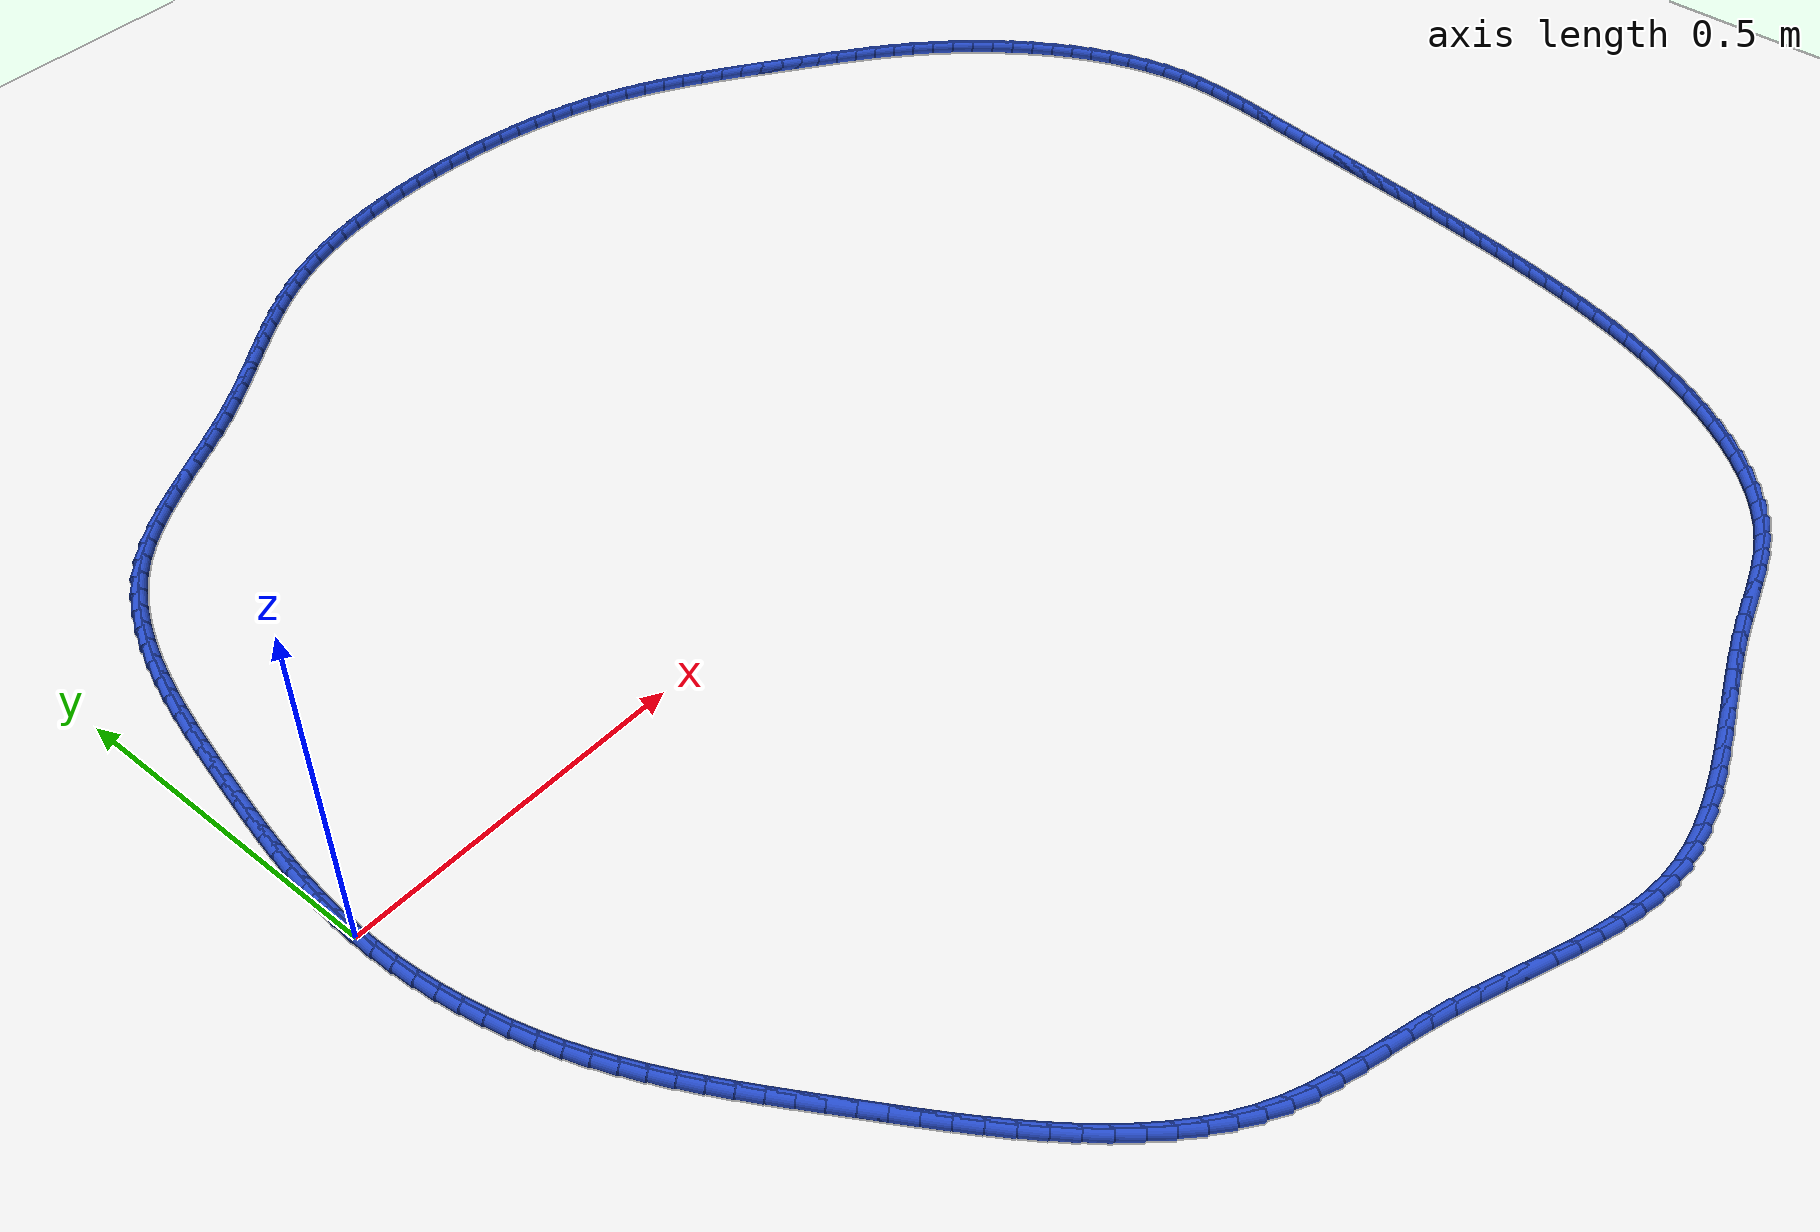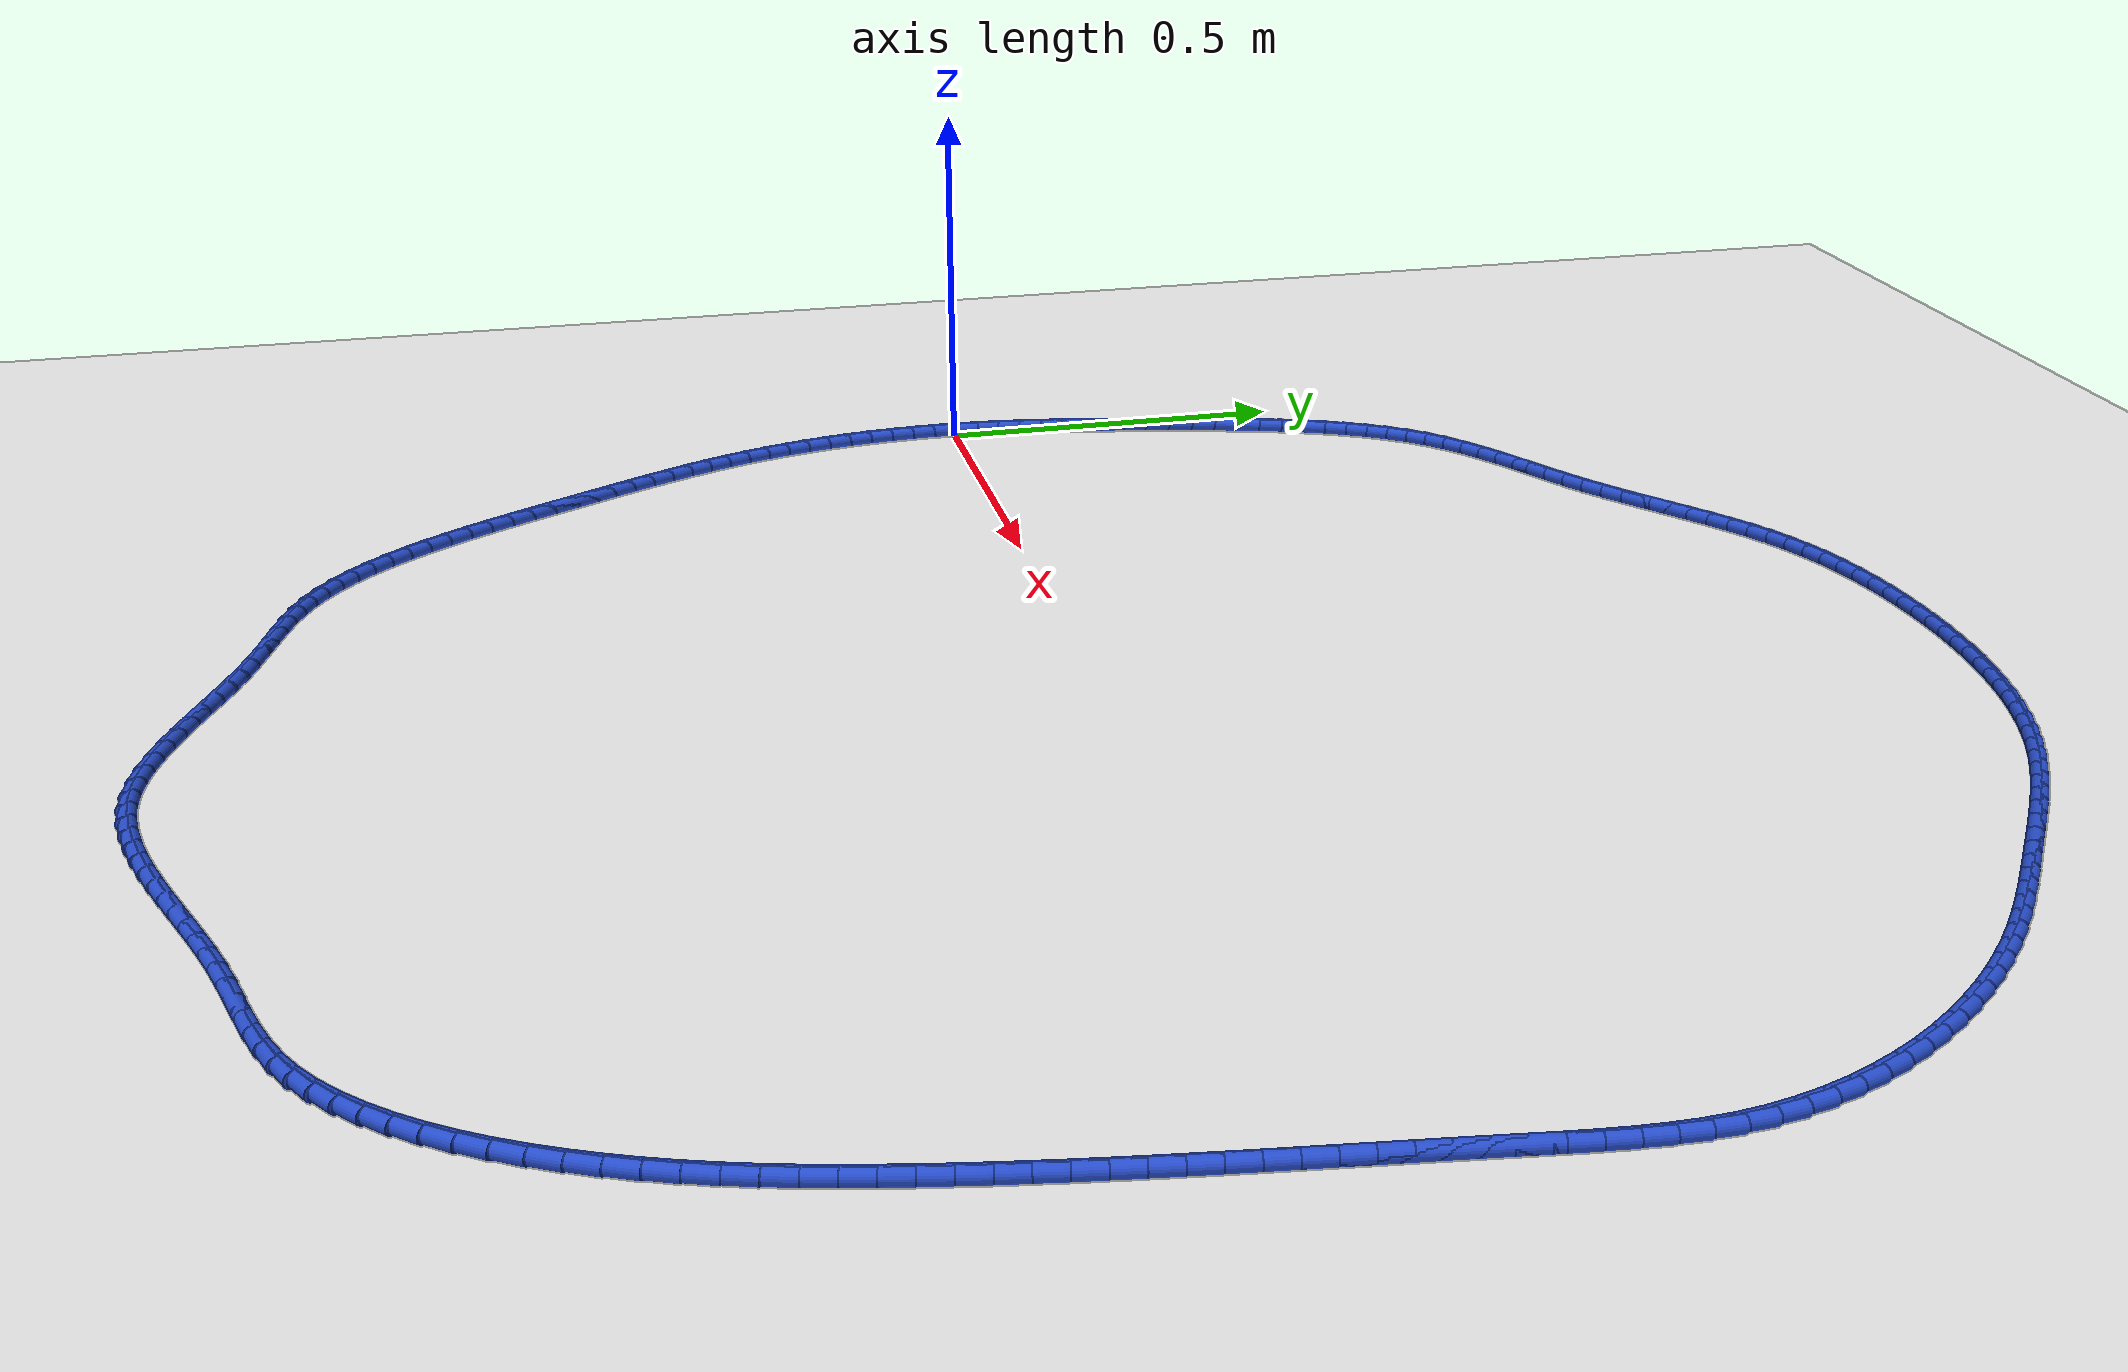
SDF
<sdf version="1.6">
 <world name="default">
  <light name="sun" type="directional">
   <pose>0 0 10 0 -0 0</pose>
   <diffuse>0.8 0.8 0.8 1</diffuse>
   <specular>0.2 0.2 0.2 1</specular>
   <attenuation>
    <range>1000</range>
    <constant>0.9</constant>
    <linear>0.01</linear>
    <quadratic>0.001</quadratic>
   </attenuation>
   <direction>-0.5 0.1 -0.9</direction>
  </light>
  <model name="ground_plane">
   <static>1</static>
   <link name="link">
    <collision name="collision">
     <geometry><plane><normal>0 0 1</normal><size>100 100</size></plane></geometry>
     <surface><friction><ode><mu>100</mu><mu2>50</mu2></ode></friction></surface>
    </collision>
    <visual name="visual">
     <cast_shadows>0</cast_shadows>
     <geometry><plane><normal>0 0 1</normal><size>100 100</size></plane></geometry>
     <material>
      <script><uri>file://media/materials/scripts/gazebo.material</uri><name>Gazebo/WhiteGlow</name></script>
     </material>
    </visual>
   </link>
  </model>
  <gravity>0 0 -9.8</gravity>
  <magnetic_field>6e-06 2.3e-05 -4.2e-05</magnetic_field>
  <atmosphere type="adiabatic"/>
  <physics name="default_physics" default="0" type="ode">
   <max_step_size>0.001</max_step_size>
   <real_time_factor>1</real_time_factor>
   <real_time_update_rate>1000</real_time_update_rate>
  </physics>
  <scene><ambient>0.4 0.4 0.4 1</ambient><background>0.7 0.7 0.7 1</background><shadows>1</shadows></scene>
  <spherical_coordinates>
   <surface_model>EARTH_WGS84</surface_model>
   <latitude_deg>0</latitude_deg>
   <longitude_deg>0</longitude_deg>
   <elevation>0</elevation>
   <heading_deg>0</heading_deg>
  </spherical_coordinates>
  <model name="line">
   <link name="link_0">
    <pose>-1.734723475976807e-17 -2.0816681711721685e-17 0.01 0 1.57 1.526959184127849</pose>
    <collision name="collision">
     <geometry><cylinder><radius>0.01</radius><length>0.08</length></cylinder></geometry>
    </collision>
    <visual name="visual">
     <material>
      <script><name>Gazebo/Blue</name><uri>file://media/materials/scripts/gazebo.material</uri></script>
     </material>
     <geometry><cylinder><radius>0.01</radius><length>0.08</length></cylinder></geometry>
    </visual>
   </link>
   <link name="link_1">
    <pose>0.0014498018781147913 0.0330512660859897 0.01 0 1.57 1.4904658622891598</pose>
    <collision name="collision">
     <geometry><cylinder><radius>0.01</radius><length>0.08</length></cylinder></geometry>
    </collision>
    <visual name="visual">
     <material>
      <script><name>Gazebo/Blue</name><uri>file://media/materials/scripts/gazebo.material</uri></script>
     </material>
     <geometry><cylinder><radius>0.01</radius><length>0.08</length></cylinder></geometry>
    </visual>
   </link>
   <link name="link_2">
    <pose>0.004095249128174418 0.06591245361064582 0.01 0 1.57 1.4576380483005305</pose>
    <collision name="collision">
     <geometry><cylinder><radius>0.01</radius><length>0.08</length></cylinder></geometry>
    </collision>
    <visual name="visual">
     <material>
      <script><name>Gazebo/Blue</name><uri>file://media/materials/scripts/gazebo.material</uri></script>
     </material>
     <geometry><cylinder><radius>0.01</radius><length>0.08</length></cylinder></geometry>
    </visual>
   </link>
   <link name="link_3">
    <pose>0.007815568139779728 0.09864913165370315 0.01 0 1.57 1.4287142719330133</pose>
    <collision name="collision">
     <geometry><cylinder><radius>0.01</radius><length>0.08</length></cylinder></geometry>
    </collision>
    <visual name="visual">
     <material>
      <script><name>Gazebo/Blue</name><uri>file://media/materials/scripts/gazebo.material</uri></script>
     </material>
     <geometry><cylinder><radius>0.01</radius><length>0.08</length></cylinder></geometry>
    </visual>
   </link>
   <link name="link_4">
    <pose>0.012489985302531603 0.13132686929489668 0.01 0 1.57 1.4038517243894906</pose>
    <collision name="collision">
     <geometry><cylinder><radius>0.01</radius><length>0.08</length></cylinder></geometry>
    </collision>
    <visual name="visual">
     <material>
      <script><name>Gazebo/Blue</name><uri>file://media/materials/scripts/gazebo.material</uri></script>
     </material>
     <geometry><cylinder><radius>0.01</radius><length>0.08</length></cylinder></geometry>
    </visual>
   </link>
   <link name="link_5">
    <pose>0.01799772700603089 0.16401123561396108 0.01 0 1.57 1.3831361687776653</pose>
    <collision name="collision">
     <geometry><cylinder><radius>0.01</radius><length>0.08</length></cylinder></geometry>
    </collision>
    <visual name="visual">
     <material>
      <script><name>Gazebo/Blue</name><uri>file://media/materials/scripts/gazebo.material</uri></script>
     </material>
     <geometry><cylinder><radius>0.01</radius><length>0.08</length></cylinder></geometry>
    </visual>
   </link>
   <link name="link_6">
    <pose>0.024218019639878463 0.1967677996906313 0.01 0 1.57 1.3665933434921467</pose>
    <collision name="collision">
     <geometry><cylinder><radius>0.01</radius><length>0.08</length></cylinder></geometry>
    </collision>
    <visual name="visual">
     <material>
      <script><name>Gazebo/Blue</name><uri>file://media/materials/scripts/gazebo.material</uri></script>
     </material>
     <geometry><cylinder><radius>0.01</radius><length>0.08</length></cylinder></geometry>
    </visual>
   </link>
   <link name="link_7">
    <pose>0.031030089593675193 0.22966213060464213 0.01 0 1.57 1.3542002880115518</pose>
    <collision name="collision">
     <geometry><cylinder><radius>0.01</radius><length>0.08</length></cylinder></geometry>
    </collision>
    <visual name="visual">
     <material>
      <script><name>Gazebo/Blue</name><uri>file://media/materials/scripts/gazebo.material</uri></script>
     </material>
     <geometry><cylinder><radius>0.01</radius><length>0.08</length></cylinder></geometry>
    </visual>
   </link>
   <link name="link_8">
    <pose>0.03831316325702195 0.2627597974357286 0.01 0 1.57 1.3458955109428532</pose>
    <collision name="collision">
     <geometry><cylinder><radius>0.01</radius><length>0.08</length></cylinder></geometry>
    </collision>
    <visual name="visual">
     <material>
      <script><name>Gazebo/Blue</name><uri>file://media/materials/scripts/gazebo.material</uri></script>
     </material>
     <geometry><cylinder><radius>0.01</radius><length>0.08</length></cylinder></geometry>
    </visual>
   </link>
   <link name="link_9">
    <pose>0.045946467019519585 0.29612636926362523 0.01 0 1.57 1.3412098617240096</pose>
    <collision name="collision">
     <geometry><cylinder><radius>0.01</radius><length>0.08</length></cylinder></geometry>
    </collision>
    <visual name="visual">
     <material>
      <script><name>Gazebo/Blue</name><uri>file://media/materials/scripts/gazebo.material</uri></script>
     </material>
     <geometry><cylinder><radius>0.01</radius><length>0.08</length></cylinder></geometry>
    </visual>
   </link>
   <link name="link_10">
    <pose>0.05382022357461497 0.32981705834143815 0.01 0 1.57 1.3347790992970308</pose>
    <collision name="collision">
     <geometry><cylinder><radius>0.01</radius><length>0.08</length></cylinder></geometry>
    </collision>
    <visual name="visual">
     <material>
      <script><name>Gazebo/Blue</name><uri>file://media/materials/scripts/gazebo.material</uri></script>
     </material>
     <geometry><cylinder><radius>0.01</radius><length>0.08</length></cylinder></geometry>
    </visual>
   </link>
   <link name="link_11">
    <pose>0.06197906936808926 0.3637416429214977 0.01 0 1.57 1.322710118944405</pose>
    <collision name="collision">
     <geometry><cylinder><radius>0.01</radius><length>0.08</length></cylinder></geometry>
    </collision>
    <visual name="visual">
     <material>
      <script><name>Gazebo/Blue</name><uri>file://media/materials/scripts/gazebo.material</uri></script>
     </material>
     <geometry><cylinder><radius>0.01</radius><length>0.08</length></cylinder></geometry>
    </visual>
   </link>
   <link name="link_12">
    <pose>0.07058153503570558 0.39770263044985055 0.01 0 1.57 1.30482518065389</pose>
    <collision name="collision">
     <geometry><cylinder><radius>0.01</radius><length>0.08</length></cylinder></geometry>
    </collision>
    <visual name="visual">
     <material>
      <script><name>Gazebo/Blue</name><uri>file://media/materials/scripts/gazebo.material</uri></script>
     </material>
     <geometry><cylinder><radius>0.01</radius><length>0.08</length></cylinder></geometry>
    </visual>
   </link>
   <link name="link_13">
    <pose>0.07978880753417798 0.43150002652683755 0.01 0 1.57 1.2809009736844716</pose>
    <collision name="collision">
     <geometry><cylinder><radius>0.01</radius><length>0.08</length></cylinder></geometry>
    </collision>
    <visual name="visual">
     <material>
      <script><name>Gazebo/Blue</name><uri>file://media/materials/scripts/gazebo.material</uri></script>
     </material>
     <geometry><cylinder><radius>0.01</radius><length>0.08</length></cylinder></geometry>
    </visual>
   </link>
   <link name="link_14">
    <pose>0.08976207382022057 0.46493383675279965 0.01 0 1.57 1.2505879785619038</pose>
    <collision name="collision">
     <geometry><cylinder><radius>0.01</radius><length>0.08</length></cylinder></geometry>
    </collision>
    <visual name="visual">
     <material>
      <script><name>Gazebo/Blue</name><uri>file://media/materials/scripts/gazebo.material</uri></script>
     </material>
     <geometry><cylinder><radius>0.01</radius><length>0.08</length></cylinder></geometry>
    </visual>
   </link>
   <link name="link_15">
    <pose>0.1006625208505474 0.4978040667280773 0.01 0 1.57 1.2134239499991615</pose>
    <collision name="collision">
     <geometry><cylinder><radius>0.01</radius><length>0.08</length></cylinder></geometry>
    </collision>
    <visual name="visual">
     <material>
      <script><name>Gazebo/Blue</name><uri>file://media/materials/scripts/gazebo.material</uri></script>
     </material>
     <geometry><cylinder><radius>0.01</radius><length>0.08</length></cylinder></geometry>
    </visual>
   </link>
   <link name="link_16">
    <pose>0.11265133558187257 0.5299107220530116 0.01 0 1.57 1.1688561181797685</pose>
    <collision name="collision">
     <geometry><cylinder><radius>0.01</radius><length>0.08</length></cylinder></geometry>
    </collision>
    <visual name="visual">
     <material>
      <script><name>Gazebo/Blue</name><uri>file://media/materials/scripts/gazebo.material</uri></script>
     </material>
     <geometry><cylinder><radius>0.01</radius><length>0.08</length></cylinder></geometry>
    </visual>
   </link>
   <link name="link_17">
    <pose>0.12588970497091015 0.5610538083279433 0.01 0 1.57 1.116280184276223</pose>
    <collision name="collision">
     <geometry><cylinder><radius>0.01</radius><length>0.08</length></cylinder></geometry>
    </collision>
    <visual name="visual">
     <material>
      <script><name>Gazebo/Blue</name><uri>file://media/materials/scripts/gazebo.material</uri></script>
     </material>
     <geometry><cylinder><radius>0.01</radius><length>0.08</length></cylinder></geometry>
    </visual>
   </link>
   <link name="link_18">
    <pose>0.14053881597437415 0.5910333311532128 0.01 0 1.57 1.05510644692636</pose>
    <collision name="collision">
     <geometry><cylinder><radius>0.01</radius><length>0.08</length></cylinder></geometry>
    </collision>
    <visual name="visual">
     <material>
      <script><name>Gazebo/Blue</name><uri>file://media/materials/scripts/gazebo.material</uri></script>
     </material>
     <geometry><cylinder><radius>0.01</radius><length>0.08</length></cylinder></geometry>
    </visual>
   </link>
   <link name="link_19">
    <pose>0.15675985554897875 0.6196492961291613 0.01 0 1.57 0.984864014666451</pose>
    <collision name="collision">
     <geometry><cylinder><radius>0.01</radius><length>0.08</length></cylinder></geometry>
    </collision>
    <visual name="visual">
     <material>
      <script><name>Gazebo/Blue</name><uri>file://media/materials/scripts/gazebo.material</uri></script>
     </material>
     <geometry><cylinder><radius>0.01</radius><length>0.08</length></cylinder></geometry>
    </visual>
   </link>
   <link name="link_20">
    <pose>0.174714010651438 0.6467017088561294 0.01 0 1.57 0.9053496829741122</pose>
    <collision name="collision">
     <geometry><cylinder><radius>0.01</radius><length>0.08</length></cylinder></geometry>
    </collision>
    <visual name="visual">
     <material>
      <script><name>Gazebo/Blue</name><uri>file://media/materials/scripts/gazebo.material</uri></script>
     </material>
     <geometry><cylinder><radius>0.01</radius><length>0.08</length></cylinder></geometry>
    </visual>
   </link>
   <link name="link_21">
    <pose>0.19456246823846585 0.6719905749344579 0.01 0 1.57 0.8168138881631174</pose>
    <collision name="collision">
     <geometry><cylinder><radius>0.01</radius><length>0.08</length></cylinder></geometry>
    </collision>
    <visual name="visual">
     <material>
      <script><name>Gazebo/Blue</name><uri>file://media/materials/scripts/gazebo.material</uri></script>
     </material>
     <geometry><cylinder><radius>0.01</radius><length>0.08</length></cylinder></geometry>
    </visual>
   </link>
   <link name="link_22">
    <pose>0.21646641526677662 0.6953158999644878 0.01 0 1.57 0.7229897747972343</pose>
    <collision name="collision">
     <geometry><cylinder><radius>0.01</radius><length>0.08</length></cylinder></geometry>
    </collision>
    <visual name="visual">
     <material>
      <script><name>Gazebo/Blue</name><uri>file://media/materials/scripts/gazebo.material</uri></script>
     </material>
     <geometry><cylinder><radius>0.01</radius><length>0.08</length></cylinder></geometry>
    </visual>
   </link>
   <link name="link_23">
    <pose>0.2405264829706774 0.7165458174239211 0.01 0 1.57 0.6409627825015399</pose>
    <collision name="collision">
     <geometry><cylinder><radius>0.01</radius><length>0.08</length></cylinder></geometry>
    </collision>
    <visual name="visual">
     <material>
      <script><name>Gazebo/Blue</name><uri>file://media/materials/scripts/gazebo.material</uri></script>
     </material>
     <geometry><cylinder><radius>0.01</radius><length>0.08</length></cylinder></geometry>
    </visual>
   </link>
   <link name="link_24">
    <pose>0.26650617566579515 0.7359277435478643 0.01 0 1.57 0.5765677331399491</pose>
    <collision name="collision">
     <geometry><cylinder><radius>0.01</radius><length>0.08</length></cylinder></geometry>
    </collision>
    <visual name="visual">
     <material>
      <script><name>Gazebo/Blue</name><uri>file://media/materials/scripts/gazebo.material</uri></script>
     </material>
     <geometry><cylinder><radius>0.01</radius><length>0.08</length></cylinder></geometry>
    </visual>
   </link>
   <link name="link_25">
    <pose>0.29405236525043665 0.7538403112212777 0.01 0 1.57 0.5292572946935187</pose>
    <collision name="collision">
     <geometry><cylinder><radius>0.01</radius><length>0.08</length></cylinder></geometry>
    </collision>
    <visual name="visual">
     <material>
      <script><name>Gazebo/Blue</name><uri>file://media/materials/scripts/gazebo.material</uri></script>
     </material>
     <geometry><cylinder><radius>0.01</radius><length>0.08</length></cylinder></geometry>
    </visual>
   </link>
   <link name="link_26">
    <pose>0.322811811224496 0.7706622797823259 0.01 0 1.57 0.49815054567101197</pose>
    <collision name="collision">
     <geometry><cylinder><radius>0.01</radius><length>0.08</length></cylinder></geometry>
    </collision>
    <visual name="visual">
     <material>
      <script><name>Gazebo/Blue</name><uri>file://media/materials/scripts/gazebo.material</uri></script>
     </material>
     <geometry><cylinder><radius>0.01</radius><length>0.08</length></cylinder></geometry>
    </visual>
   </link>
   <link name="link_27">
    <pose>0.3524312730878677 0.786772408569174 0.01 0 1.57 0.4824257304712187</pose>
    <collision name="collision">
     <geometry><cylinder><radius>0.01</radius><length>0.08</length></cylinder></geometry>
    </collision>
    <visual name="visual">
     <material>
      <script><name>Gazebo/Blue</name><uri>file://media/materials/scripts/gazebo.material</uri></script>
     </material>
     <geometry><cylinder><radius>0.01</radius><length>0.08</length></cylinder></geometry>
    </visual>
   </link>
   <link name="link_28">
    <pose>0.3825575103404464 0.8025494569199867 0.01 0 1.57 0.4815252766576677</pose>
    <collision name="collision">
     <geometry><cylinder><radius>0.01</radius><length>0.08</length></cylinder></geometry>
    </collision>
    <visual name="visual">
     <material>
      <script><name>Gazebo/Blue</name><uri>file://media/materials/scripts/gazebo.material</uri></script>
     </material>
     <geometry><cylinder><radius>0.01</radius><length>0.08</length></cylinder></geometry>
    </visual>
   </link>
   <link name="link_29">
    <pose>0.4128372824821262 0.818372184172929 0.01 0 1.57 0.4952344014103675</pose>
    <collision name="collision">
     <geometry><cylinder><radius>0.01</radius><length>0.08</length></cylinder></geometry>
    </collision>
    <visual name="visual">
     <material>
      <script><name>Gazebo/Blue</name><uri>file://media/materials/scripts/gazebo.material</uri></script>
     </material>
     <geometry><cylinder><radius>0.01</radius><length>0.08</length></cylinder></geometry>
    </visual>
   </link>
   <link name="link_30">
    <pose>0.4429173490128021 0.834619349666166 0.01 0 1.57 0.5236563129942602</pose>
    <collision name="collision">
     <geometry><cylinder><radius>0.01</radius><length>0.08</length></cylinder></geometry>
    </collision>
    <visual name="visual">
     <material>
      <script><name>Gazebo/Blue</name><uri>file://media/materials/scripts/gazebo.material</uri></script>
     </material>
     <geometry><cylinder><radius>0.01</radius><length>0.08</length></cylinder></geometry>
    </visual>
   </link>
   <link name="link_31">
    <pose>0.47244479630320724 0.8516692946262538 0.01 0 1.57 0.5605959052362508</pose>
    <collision name="collision">
     <geometry><cylinder><radius>0.01</radius><length>0.08</length></cylinder></geometry>
    </collision>
    <visual name="visual">
     <material>
      <script><name>Gazebo/Blue</name><uri>file://media/materials/scripts/gazebo.material</uri></script>
     </material>
     <geometry><cylinder><radius>0.01</radius><length>0.08</length></cylinder></geometry>
    </visual>
   </link>
   <link name="link_32">
    <pose>0.50120452542109 0.8697240768129104 0.01 0 1.57 0.5894997116436339</pose>
    <collision name="collision">
     <geometry><cylinder><radius>0.01</radius><length>0.08</length></cylinder></geometry>
    </collision>
    <visual name="visual">
     <material>
      <script><name>Gazebo/Blue</name><uri>file://media/materials/scripts/gazebo.material</uri></script>
     </material>
     <geometry><cylinder><radius>0.01</radius><length>0.08</length></cylinder></geometry>
    </visual>
   </link>
   <link name="link_33">
    <pose>0.5293323720646942 0.8885368615626432 0.01 0 1.57 0.6076348891645273</pose>
    <collision name="collision">
     <geometry><cylinder><radius>0.01</radius><length>0.08</length></cylinder></geometry>
    </collision>
    <visual name="visual">
     <material>
      <script><name>Gazebo/Blue</name><uri>file://media/materials/scripts/gazebo.material</uri></script>
     </material>
     <geometry><cylinder><radius>0.01</radius><length>0.08</length></cylinder></geometry>
    </visual>
   </link>
   <link name="link_34">
    <pose>0.5570192137686502 0.9077904083267422 0.01 0 1.57 0.6149055852538204</pose>
    <collision name="collision">
     <geometry><cylinder><radius>0.01</radius><length>0.08</length></cylinder></geometry>
    </collision>
    <visual name="visual">
     <material>
      <script><name>Gazebo/Blue</name><uri>file://media/materials/scripts/gazebo.material</uri></script>
     </material>
     <geometry><cylinder><radius>0.01</radius><length>0.08</length></cylinder></geometry>
    </visual>
   </link>
   <link name="link_35">
    <pose>0.5844559280675876 0.9271674765564978 0.01 0 1.57 0.6111946242654754</pose>
    <collision name="collision">
     <geometry><cylinder><radius>0.01</radius><length>0.08</length></cylinder></geometry>
    </collision>
    <visual name="visual">
     <material>
      <script><name>Gazebo/Blue</name><uri>file://media/materials/scripts/gazebo.material</uri></script>
     </material>
     <geometry><cylinder><radius>0.01</radius><length>0.08</length></cylinder></geometry>
    </visual>
   </link>
   <link name="link_36">
    <pose>0.611833392496136 0.9463508257031996 0.01 0 1.57 0.5963361657831775</pose>
    <collision name="collision">
     <geometry><cylinder><radius>0.01</radius><length>0.08</length></cylinder></geometry>
    </collision>
    <visual name="visual">
     <material>
      <script><name>Gazebo/Blue</name><uri>file://media/materials/scripts/gazebo.material</uri></script>
     </material>
     <geometry><cylinder><radius>0.01</radius><length>0.08</length></cylinder></geometry>
    </visual>
   </link>
   <link name="link_37">
    <pose>0.6393424845889257 0.9650232152181385 0.01 0 1.57 0.5701275995311553</pose>
    <collision name="collision">
     <geometry><cylinder><radius>0.01</radius><length>0.08</length></cylinder></geometry>
    </collision>
    <visual name="visual">
     <material>
      <script><name>Gazebo/Blue</name><uri>file://media/materials/scripts/gazebo.material</uri></script>
     </material>
     <geometry><cylinder><radius>0.01</radius><length>0.08</length></cylinder></geometry>
    </visual>
   </link>
   <link name="link_38">
    <pose>0.6671740818805866 0.9828674045526041 0.01 0 1.57 0.5323851207484867</pose>
    <collision name="collision">
     <geometry><cylinder><radius>0.01</radius><length>0.08</length></cylinder></geometry>
    </collision>
    <visual name="visual">
     <material>
      <script><name>Gazebo/Blue</name><uri>file://media/materials/scripts/gazebo.material</uri></script>
     </material>
     <geometry><cylinder><radius>0.01</radius><length>0.08</length></cylinder></geometry>
    </visual>
   </link>
   <link name="link_39">
    <pose>0.6955190619057483 0.9995661531578873 0.01 0 1.57 0.4830479582796917</pose>
    <collision name="collision">
     <geometry><cylinder><radius>0.01</radius><length>0.08</length></cylinder></geometry>
    </collision>
    <visual name="visual">
     <material>
      <script><name>Gazebo/Blue</name><uri>file://media/materials/scripts/gazebo.material</uri></script>
     </material>
     <geometry><cylinder><radius>0.01</radius><length>0.08</length></cylinder></geometry>
    </visual>
   </link>
   <link name="link_40">
    <pose>0.7245683021990408 1.0148022204852776 0.01 0 1.57 0.42286842526191754</pose>
    <collision name="collision">
     <geometry><cylinder><radius>0.01</radius><length>0.08</length></cylinder></geometry>
    </collision>
    <visual name="visual">
     <material>
      <script><name>Gazebo/Blue</name><uri>file://media/materials/scripts/gazebo.material</uri></script>
     </material>
     <geometry><cylinder><radius>0.01</radius><length>0.08</length></cylinder></geometry>
    </visual>
   </link>
   <link name="link_41">
    <pose>0.7545020701609287 1.0282729379728412 0.01 0 1.57 0.3605038200546781</pose>
    <collision name="collision">
     <geometry><cylinder><radius>0.01</radius><length>0.08</length></cylinder></geometry>
    </collision>
    <visual name="visual">
     <material>
      <script><name>Gazebo/Blue</name><uri>file://media/materials/scripts/gazebo.material</uri></script>
     </material>
     <geometry><cylinder><radius>0.01</radius><length>0.08</length></cylinder></geometry>
    </visual>
   </link>
   <link name="link_42">
    <pose>0.7853389071202563 1.039897752080008 0.01 0 1.57 0.30249084022194517</pose>
    <collision name="collision">
     <geometry><cylinder><radius>0.01</radius><length>0.08</length></cylinder></geometry>
    </collision>
    <visual name="visual">
     <material>
      <script><name>Gazebo/Blue</name><uri>file://media/materials/scripts/gazebo.material</uri></script>
     </material>
     <geometry><cylinder><radius>0.01</radius><length>0.08</length></cylinder></geometry>
    </visual>
   </link>
   <link name="link_43">
    <pose>0.8169713222094616 1.049769202223437 0.01 0 1.57 0.24893282365428235</pose>
    <collision name="collision">
     <geometry><cylinder><radius>0.01</radius><length>0.08</length></cylinder></geometry>
    </collision>
    <visual name="visual">
     <material>
      <script><name>Gazebo/Blue</name><uri>file://media/materials/scripts/gazebo.material</uri></script>
     </material>
     <geometry><cylinder><radius>0.01</radius><length>0.08</length></cylinder></geometry>
    </visual>
   </link>
   <link name="link_44">
    <pose>0.8492884926482439 1.0579844038776969 0.01 0 1.57 0.19967032997633932</pose>
    <collision name="collision">
     <geometry><cylinder><radius>0.01</radius><length>0.08</length></cylinder></geometry>
    </collision>
    <visual name="visual">
     <material>
      <script><name>Gazebo/Blue</name><uri>file://media/materials/scripts/gazebo.material</uri></script>
     </material>
     <geometry><cylinder><radius>0.01</radius><length>0.08</length></cylinder></geometry>
    </visual>
   </link>
   <link name="link_45">
    <pose>0.8821795956563026 1.0646404725173548 0.01 0 1.57 0.1544832267433729</pose>
    <collision name="collision">
     <geometry><cylinder><radius>0.01</radius><length>0.08</length></cylinder></geometry>
    </collision>
    <visual name="visual">
     <material>
      <script><name>Gazebo/Blue</name><uri>file://media/materials/scripts/gazebo.material</uri></script>
     </material>
     <geometry><cylinder><radius>0.01</radius><length>0.08</length></cylinder></geometry>
    </visual>
   </link>
   <link name="link_46">
    <pose>0.9155338084533374 1.0698345236169784 0.01 0 1.57 0.1131177367026334</pose>
    <collision name="collision">
     <geometry><cylinder><radius>0.01</radius><length>0.08</length></cylinder></geometry>
    </collision>
    <visual name="visual">
     <material>
      <script><name>Gazebo/Blue</name><uri>file://media/materials/scripts/gazebo.material</uri></script>
     </material>
     <geometry><cylinder><radius>0.01</radius><length>0.08</length></cylinder></geometry>
    </visual>
   </link>
   <link name="link_47">
    <pose>0.9492403082590476 1.0736636726511357 0.01 0 1.57 0.07530698040194173</pose>
    <collision name="collision">
     <geometry><cylinder><radius>0.01</radius><length>0.08</length></cylinder></geometry>
    </collision>
    <visual name="visual">
     <material>
      <script><name>Gazebo/Blue</name><uri>file://media/materials/scripts/gazebo.material</uri></script>
     </material>
     <geometry><cylinder><radius>0.01</radius><length>0.08</length></cylinder></geometry>
    </visual>
   </link>
   <link name="link_48">
    <pose>0.9831882722931327 1.076225035094394 0.01 0 1.57 0.04078570984300851</pose>
    <collision name="collision">
     <geometry><cylinder><radius>0.01</radius><length>0.08</length></cylinder></geometry>
    </collision>
    <visual name="visual">
     <material>
      <script><name>Gazebo/Blue</name><uri>file://media/materials/scripts/gazebo.material</uri></script>
     </material>
     <geometry><cylinder><radius>0.01</radius><length>0.08</length></cylinder></geometry>
    </visual>
   </link>
   <link name="link_49">
    <pose>1.0172668777752925 1.077615726421321 0.01 0 1.57 0.009245487454102821</pose>
    <collision name="collision">
     <geometry><cylinder><radius>0.01</radius><length>0.08</length></cylinder></geometry>
    </collision>
    <visual name="visual">
     <material>
      <script><name>Gazebo/Blue</name><uri>file://media/materials/scripts/gazebo.material</uri></script>
     </material>
     <geometry><cylinder><radius>0.01</radius><length>0.08</length></cylinder></geometry>
    </visual>
   </link>
   <link name="link_50">
    <pose>1.0513661584555287 1.077930999876186 0.01 0 1.57 -0.02122348295904273</pose>
    <collision name="collision">
     <geometry><cylinder><radius>0.01</radius><length>0.08</length></cylinder></geometry>
    </collision>
    <visual name="visual">
     <material>
      <script><name>Gazebo/Blue</name><uri>file://media/materials/scripts/gazebo.material</uri></script>
     </material>
     <geometry><cylinder><radius>0.01</radius><length>0.08</length></cylinder></geometry>
    </visual>
   </link>
   <link name="link_51">
    <pose>1.085402636489084 1.0772085187841778 0.01 0 1.57 -0.05271455473331886</pose>
    <collision name="collision">
     <geometry><cylinder><radius>0.01</radius><length>0.08</length></cylinder></geometry>
    </collision>
    <visual name="visual">
     <material>
      <script><name>Gazebo/Blue</name><uri>file://media/materials/scripts/gazebo.material</uri></script>
     </material>
     <geometry><cylinder><radius>0.01</radius><length>0.08</length></cylinder></geometry>
    </visual>
   </link>
   <link name="link_52">
    <pose>1.1193237528744733 1.075418724089008 0.01 0 1.57 -0.0854226394720076</pose>
    <collision name="collision">
     <geometry><cylinder><radius>0.01</radius><length>0.08</length></cylinder></geometry>
    </collision>
    <visual name="visual">
     <material>
      <script><name>Gazebo/Blue</name><uri>file://media/materials/scripts/gazebo.material</uri></script>
     </material>
     <geometry><cylinder><radius>0.01</radius><length>0.08</length></cylinder></geometry>
    </visual>
   </link>
   <link name="link_53">
    <pose>1.1530786978774576 1.0725282535549043 0.01 0 1.57 -0.11942754282316366</pose>
    <collision name="collision">
     <geometry><cylinder><radius>0.01</radius><length>0.08</length></cylinder></geometry>
    </collision>
    <visual name="visual">
     <material>
      <script><name>Gazebo/Blue</name><uri>file://media/materials/scripts/gazebo.material</uri></script>
     </material>
     <geometry><cylinder><radius>0.01</radius><length>0.08</length></cylinder></geometry>
    </visual>
   </link>
   <link name="link_54">
    <pose>1.1866166617637999 1.0685037449460948 0.01 0 1.57 -0.15480439020922973</pose>
    <collision name="collision">
     <geometry><cylinder><radius>0.01</radius><length>0.08</length></cylinder></geometry>
    </collision>
    <visual name="visual">
     <material>
      <script><name>Gazebo/Blue</name><uri>file://media/materials/scripts/gazebo.material</uri></script>
     </material>
     <geometry><cylinder><radius>0.01</radius><length>0.08</length></cylinder></geometry>
    </visual>
   </link>
   <link name="link_55">
    <pose>1.2198868347992622 1.063311836026808 0.01 0 1.57 -0.19162167110095227</pose>
    <collision name="collision">
     <geometry><cylinder><radius>0.01</radius><length>0.08</length></cylinder></geometry>
    </collision>
    <visual name="visual">
     <material>
      <script><name>Gazebo/Blue</name><uri>file://media/materials/scripts/gazebo.material</uri></script>
     </material>
     <geometry><cylinder><radius>0.01</radius><length>0.08</length></cylinder></geometry>
    </visual>
   </link>
   <link name="link_56">
    <pose>1.2528384072496075 1.0569191645612717 0.01 0 1.57 -0.22993887479623012</pose>
    <collision name="collision">
     <geometry><cylinder><radius>0.01</radius><length>0.08</length></cylinder></geometry>
    </collision>
    <visual name="visual">
     <material>
      <script><name>Gazebo/Blue</name><uri>file://media/materials/scripts/gazebo.material</uri></script>
     </material>
     <geometry><cylinder><radius>0.01</radius><length>0.08</length></cylinder></geometry>
    </visual>
   </link>
   <link name="link_57">
    <pose>1.2854205693805976 1.0492923683137143 0.01 0 1.57 -0.2698037209241004</pose>
    <collision name="collision">
     <geometry><cylinder><radius>0.01</radius><length>0.08</length></cylinder></geometry>
    </collision>
    <visual name="visual">
     <material>
      <script><name>Gazebo/Blue</name><uri>file://media/materials/scripts/gazebo.material</uri></script>
     </material>
     <geometry><cylinder><radius>0.01</radius><length>0.08</length></cylinder></geometry>
    </visual>
   </link>
   <link name="link_58">
    <pose>1.3175825114579949 1.0403980850483643 0.01 0 1.57 -0.31124902055332937</pose>
    <collision name="collision">
     <geometry><cylinder><radius>0.01</radius><length>0.08</length></cylinder></geometry>
    </collision>
    <visual name="visual">
     <material>
      <script><name>Gazebo/Blue</name><uri>file://media/materials/scripts/gazebo.material</uri></script>
     </material>
     <geometry><cylinder><radius>0.01</radius><length>0.08</length></cylinder></geometry>
    </visual>
   </link>
   <link name="link_59">
    <pose>1.3492734237475623 1.0302029525294496 0.01 0 1.57 -0.35428924825967656</pose>
    <collision name="collision">
     <geometry><cylinder><radius>0.01</radius><length>0.08</length></cylinder></geometry>
    </collision>
    <visual name="visual">
     <material>
      <script><name>Gazebo/Blue</name><uri>file://media/materials/scripts/gazebo.material</uri></script>
     </material>
     <geometry><cylinder><radius>0.01</radius><length>0.08</length></cylinder></geometry>
    </visual>
   </link>
   <link name="link_60">
    <pose>1.3804424965150621 1.0186736085211985 0.01 0 1.57 -0.39891696124763515</pose>
    <collision name="collision">
     <geometry><cylinder><radius>0.01</radius><length>0.08</length></cylinder></geometry>
    </collision>
    <visual name="visual">
     <material>
      <script><name>Gazebo/Blue</name><uri>file://media/materials/scripts/gazebo.material</uri></script>
     </material>
     <geometry><cylinder><radius>0.01</radius><length>0.08</length></cylinder></geometry>
    </visual>
   </link>
   <link name="link_61">
    <pose>1.4110389200262567 1.0057766907878396 0.01 0 1.57 -0.44425029999144644</pose>
    <collision name="collision">
     <geometry><cylinder><radius>0.01</radius><length>0.08</length></cylinder></geometry>
    </collision>
    <visual name="visual">
     <material>
      <script><name>Gazebo/Blue</name><uri>file://media/materials/scripts/gazebo.material</uri></script>
     </material>
     <geometry><cylinder><radius>0.01</radius><length>0.08</length></cylinder></geometry>
    </visual>
   </link>
   <link name="link_62">
    <pose>1.4410254931771402 0.9915035833022187 0.01 0 1.57 -0.48528868936568276</pose>
    <collision name="collision">
     <geometry><cylinder><radius>0.01</radius><length>0.08</length></cylinder></geometry>
    </collision>
    <visual name="visual">
     <material>
      <script><name>Gazebo/Blue</name><uri>file://media/materials/scripts/gazebo.material</uri></script>
     </material>
     <geometry><cylinder><radius>0.01</radius><length>0.08</length></cylinder></geometry>
    </visual>
   </link>
   <link name="link_63">
    <pose>1.4704441658554785 0.9759895998024445 0.01 0 1.57 -0.520219605334575</pose>
    <collision name="collision">
     <geometry><cylinder><radius>0.01</radius><length>0.08</length></cylinder></geometry>
    </collision>
    <visual name="visual">
     <material>
      <script><name>Gazebo/Blue</name><uri>file://media/materials/scripts/gazebo.material</uri></script>
     </material>
     <geometry><cylinder><radius>0.01</radius><length>0.08</length></cylinder></geometry>
    </visual>
   </link>
   <link name="link_64">
    <pose>1.4993654291470226 0.9594219539186444 0.01 0 1.57 -0.5490804780549143</pose>
    <collision name="collision">
     <geometry><cylinder><radius>0.01</radius><length>0.08</length></cylinder></geometry>
    </collision>
    <visual name="visual">
     <material>
      <script><name>Gazebo/Blue</name><uri>file://media/materials/scripts/gazebo.material</uri></script>
     </material>
     <geometry><cylinder><radius>0.01</radius><length>0.08</length></cylinder></geometry>
    </visual>
   </link>
   <link name="link_65">
    <pose>1.5278598124123044 0.9419879288805798 0.01 0 1.57 -0.5719504607172513</pose>
    <collision name="collision">
     <geometry><cylinder><radius>0.01</radius><length>0.08</length></cylinder></geometry>
    </collision>
    <visual name="visual">
     <material>
      <script><name>Gazebo/Blue</name><uri>file://media/materials/scripts/gazebo.material</uri></script>
     </material>
     <geometry><cylinder><radius>0.01</radius><length>0.08</length></cylinder></geometry>
    </visual>
   </link>
   <link name="link_66">
    <pose>1.5559978450118537 0.9238748079180121 0.01 0 1.57 -0.5889165850855029</pose>
    <collision name="collision">
     <geometry><cylinder><radius>0.01</radius><length>0.08</length></cylinder></geometry>
    </collision>
    <visual name="visual">
     <material>
      <script><name>Gazebo/Blue</name><uri>file://media/materials/scripts/gazebo.material</uri></script>
     </material>
     <geometry><cylinder><radius>0.01</radius><length>0.08</length></cylinder></geometry>
    </visual>
   </link>
   <link name="link_67">
    <pose>1.5838500563062021 0.9052698742607028 0.01 0 1.57 -0.6000500159475107</pose>
    <collision name="collision">
     <geometry><cylinder><radius>0.01</radius><length>0.08</length></cylinder></geometry>
    </collision>
    <visual name="visual">
     <material>
      <script><name>Gazebo/Blue</name><uri>file://media/materials/scripts/gazebo.material</uri></script>
     </material>
     <geometry><cylinder><radius>0.01</radius><length>0.08</length></cylinder></geometry>
    </visual>
   </link>
   <link name="link_68">
    <pose>1.61148697565588 0.8863604111384132 0.01 0 1.57 -0.6053891901506766</pose>
    <collision name="collision">
     <geometry><cylinder><radius>0.01</radius><length>0.08</length></cylinder></geometry>
    </collision>
    <visual name="visual">
     <material>
      <script><name>Gazebo/Blue</name><uri>file://media/materials/scripts/gazebo.material</uri></script>
     </material>
     <geometry><cylinder><radius>0.01</radius><length>0.08</length></cylinder></geometry>
    </visual>
   </link>
   <link name="link_69">
    <pose>1.6389791324214178 0.8673337017809047 0.01 0 1.57 -0.6056868802864507</pose>
    <collision name="collision">
     <geometry><cylinder><radius>0.01</radius><length>0.08</length></cylinder></geometry>
    </collision>
    <visual name="visual">
     <material>
      <script><name>Gazebo/Blue</name><uri>file://media/materials/scripts/gazebo.material</uri></script>
     </material>
     <geometry><cylinder><radius>0.01</radius><length>0.08</length></cylinder></geometry>
    </visual>
   </link>
   <link name="link_70">
    <pose>1.666387361379235 0.848353007337903 0.01 0 1.57 -0.6081983665845118</pose>
    <collision name="collision">
     <geometry><cylinder><radius>0.01</radius><length>0.08</length></cylinder></geometry>
    </collision>
    <visual name="visual">
     <material>
      <script><name>Gazebo/Blue</name><uri>file://media/materials/scripts/gazebo.material</uri></script>
     </material>
     <geometry><cylinder><radius>0.01</radius><length>0.08</length></cylinder></geometry>
    </visual>
   </link>
   <link name="link_71">
    <pose>1.6936794881194939 0.829351122743111 0.01 0 1.57 -0.6169963698731339</pose>
    <collision name="collision">
     <geometry><cylinder><radius>0.01</radius><length>0.08</length></cylinder></geometry>
    </collision>
    <visual name="visual">
     <material>
      <script><name>Gazebo/Blue</name><uri>file://media/materials/scripts/gazebo.material</uri></script>
     </material>
     <geometry><cylinder><radius>0.01</radius><length>0.08</length></cylinder></geometry>
    </visual>
   </link>
   <link name="link_72">
    <pose>1.7207715261775949 0.8101324585341704 0.01 0 1.57 -0.6321095713628452</pose>
    <collision name="collision">
     <geometry><cylinder><radius>0.01</radius><length>0.08</length></cylinder></geometry>
    </collision>
    <visual name="visual">
     <material>
      <script><name>Gazebo/Blue</name><uri>file://media/materials/scripts/gazebo.material</uri></script>
     </material>
     <geometry><cylinder><radius>0.01</radius><length>0.08</length></cylinder></geometry>
    </visual>
   </link>
   <link name="link_73">
    <pose>1.7475789288761476 0.7905000371049561 0.01 0 1.57 -0.6534595711522786</pose>
    <collision name="collision">
     <geometry><cylinder><radius>0.01</radius><length>0.08</length></cylinder></geometry>
    </collision>
    <visual name="visual">
     <material>
      <script><name>Gazebo/Blue</name><uri>file://media/materials/scripts/gazebo.material</uri></script>
     </material>
     <geometry><cylinder><radius>0.01</radius><length>0.08</length></cylinder></geometry>
    </visual>
   </link>
   <link name="link_74">
    <pose>1.7740171495377604 0.7702568808493422 0.01 0 1.57 -0.6808885350943154</pose>
    <collision name="collision">
     <geometry><cylinder><radius>0.01</radius><length>0.08</length></cylinder></geometry>
    </collision>
    <visual name="visual">
     <material>
      <script><name>Gazebo/Blue</name><uri>file://media/materials/scripts/gazebo.material</uri></script>
     </material>
     <geometry><cylinder><radius>0.01</radius><length>0.08</length></cylinder></geometry>
    </visual>
   </link>
   <link name="link_75">
    <pose>1.8000016414850424 0.7492060121612029 0.01 0 1.57 -0.7141394193240267</pose>
    <collision name="collision">
     <geometry><cylinder><radius>0.01</radius><length>0.08</length></cylinder></geometry>
    </collision>
    <visual name="visual">
     <material>
      <script><name>Gazebo/Blue</name><uri>file://media/materials/scripts/gazebo.material</uri></script>
     </material>
     <geometry><cylinder><radius>0.01</radius><length>0.08</length></cylinder></geometry>
    </visual>
   </link>
   <link name="link_76">
    <pose>1.825447858040602 0.7271504534344123 0.01 0 1.57 -0.7525283345865966</pose>
    <collision name="collision">
     <geometry><cylinder><radius>0.01</radius><length>0.08</length></cylinder></geometry>
    </collision>
    <visual name="visual">
     <material>
      <script><name>Gazebo/Blue</name><uri>file://media/materials/scripts/gazebo.material</uri></script>
     </material>
     <geometry><cylinder><radius>0.01</radius><length>0.08</length></cylinder></geometry>
    </visual>
   </link>
   <link name="link_77">
    <pose>1.8502676862733591 0.7039108980764806 0.01 0 1.57 -0.7929318902597442</pose>
    <collision name="collision">
     <geometry><cylinder><radius>0.01</radius><length>0.08</length></cylinder></geometry>
    </collision>
    <visual name="visual">
     <material>
      <script><name>Gazebo/Blue</name><uri>file://media/materials/scripts/gazebo.material</uri></script>
     </material>
     <geometry><cylinder><radius>0.01</radius><length>0.08</length></cylinder></geometry>
    </visual>
   </link>
   <link name="link_78">
    <pose>1.8743396209623524 0.6794735004130467 0.01 0 1.57 -0.8340721807287838</pose>
    <collision name="collision">
     <geometry><cylinder><radius>0.01</radius><length>0.08</length></cylinder></geometry>
    </collision>
    <visual name="visual">
     <material>
      <script><name>Gazebo/Blue</name><uri>file://media/materials/scripts/gazebo.material</uri></script>
     </material>
     <geometry><cylinder><radius>0.01</radius><length>0.08</length></cylinder></geometry>
    </visual>
   </link>
   <link name="link_79">
    <pose>1.8975239124466154 0.6539148171292511 0.01 0 1.57 -0.876325039428879</pose>
    <collision name="collision">
     <geometry><cylinder><radius>0.01</radius><length>0.08</length></cylinder></geometry>
    </collision>
    <visual name="visual">
     <material>
      <script><name>Gazebo/Blue</name><uri>file://media/materials/scripts/gazebo.material</uri></script>
     </material>
     <geometry><cylinder><radius>0.01</radius><length>0.08</length></cylinder></geometry>
    </visual>
   </link>
   <link name="link_80">
    <pose>1.9196806259288803 0.6273123222723715 0.01 0 1.57 -0.9200782778044176</pose>
    <collision name="collision">
     <geometry><cylinder><radius>0.01</radius><length>0.08</length></cylinder></geometry>
    </collision>
    <visual name="visual">
     <material>
      <script><name>Gazebo/Blue</name><uri>file://media/materials/scripts/gazebo.material</uri></script>
     </material>
     <geometry><cylinder><radius>0.01</radius><length>0.08</length></cylinder></geometry>
    </visual>
   </link>
   <link name="link_81">
    <pose>1.9406698266118791 0.5997434898896862 0.01 0 1.57 -0.9657204609486352</pose>
    <collision name="collision">
     <geometry><cylinder><radius>0.01</radius><length>0.08</length></cylinder></geometry>
    </collision>
    <visual name="visual">
     <material>
      <script><name>Gazebo/Blue</name><uri>file://media/materials/scripts/gazebo.material</uri></script>
     </material>
     <geometry><cylinder><radius>0.01</radius><length>0.08</length></cylinder></geometry>
    </visual>
   </link>
   <link name="link_82">
    <pose>1.9603515796983433 0.5712857940284726 0.01 0 1.57 -1.0136431384454847</pose>
    <collision name="collision">
     <geometry><cylinder><radius>0.01</radius><length>0.08</length></cylinder></geometry>
    </collision>
    <visual name="visual">
     <material>
      <script><name>Gazebo/Blue</name><uri>file://media/materials/scripts/gazebo.material</uri></script>
     </material>
     <geometry><cylinder><radius>0.01</radius><length>0.08</length></cylinder></geometry>
    </visual>
   </link>
   <link name="link_83">
    <pose>1.9785859503910033 0.5420167087360086 0.01 0 1.57 -1.0642399744052824</pose>
    <collision name="collision">
     <geometry><cylinder><radius>0.01</radius><length>0.08</length></cylinder></geometry>
    </collision>
    <visual name="visual">
     <material>
      <script><name>Gazebo/Blue</name><uri>file://media/materials/scripts/gazebo.material</uri></script>
     </material>
     <geometry><cylinder><radius>0.01</radius><length>0.08</length></cylinder></geometry>
    </visual>
   </link>
   <link name="link_84">
    <pose>1.995233003892592 0.5120137080595726 0.01 0 1.57 -1.1179018857047152</pose>
    <collision name="collision">
     <geometry><cylinder><radius>0.01</radius><length>0.08</length></cylinder></geometry>
    </collision>
    <visual name="visual">
     <material>
      <script><name>Gazebo/Blue</name><uri>file://media/materials/scripts/gazebo.material</uri></script>
     </material>
     <geometry><cylinder><radius>0.01</radius><length>0.08</length></cylinder></geometry>
    </visual>
   </link>
   <link name="link_85">
    <pose>2.0101528054058413 0.48135426604644205 0.01 0 1.57 -1.175007010932793</pose>
    <collision name="collision">
     <geometry><cylinder><radius>0.01</radius><length>0.08</length></cylinder></geometry>
    </collision>
    <visual name="visual">
     <material>
      <script><name>Gazebo/Blue</name><uri>file://media/materials/scripts/gazebo.material</uri></script>
     </material>
     <geometry><cylinder><radius>0.01</radius><length>0.08</length></cylinder></geometry>
    </visual>
   </link>
   <link name="link_86">
    <pose>2.023205420133483 0.450115856743895 0.01 0 1.57 -1.2359041561287163</pose>
    <collision name="collision">
     <geometry><cylinder><radius>0.01</radius><length>0.08</length></cylinder></geometry>
    </collision>
    <visual name="visual">
     <material>
      <script><name>Gazebo/Blue</name><uri>file://media/materials/scripts/gazebo.material</uri></script>
     </material>
     <geometry><cylinder><radius>0.01</radius><length>0.08</length></cylinder></geometry>
    </visual>
   </link>
   <link name="link_87">
    <pose>2.0342509132782483 0.4183759541992094 0.01 0 1.57 -1.3008884598681274</pose>
    <collision name="collision">
     <geometry><cylinder><radius>0.01</radius><length>0.08</length></cylinder></geometry>
    </collision>
    <visual name="visual">
     <material>
      <script><name>Gazebo/Blue</name><uri>file://media/materials/scripts/gazebo.material</uri></script>
     </material>
     <geometry><cylinder><radius>0.01</radius><length>0.08</length></cylinder></geometry>
    </visual>
   </link>
   <link name="link_88">
    <pose>2.043149350042869 0.38621203245966323 0.01 0 1.57 -1.370168638028922</pose>
    <collision name="collision">
     <geometry><cylinder><radius>0.01</radius><length>0.08</length></cylinder></geometry>
    </collision>
    <visual name="visual">
     <material>
      <script><name>Gazebo/Blue</name><uri>file://media/materials/scripts/gazebo.material</uri></script>
     </material>
     <geometry><cylinder><radius>0.01</radius><length>0.08</length></cylinder></geometry>
    </visual>
   </link>
   <link name="link_89">
    <pose>2.049760795630077 0.35370156557253424 0.01 0 1.57 -1.4438222022135072</pose>
    <collision name="collision">
     <geometry><cylinder><radius>0.01</radius><length>0.08</length></cylinder></geometry>
    </collision>
    <visual name="visual">
     <material>
      <script><name>Gazebo/Blue</name><uri>file://media/materials/scripts/gazebo.material</uri></script>
     </material>
     <geometry><cylinder><radius>0.01</radius><length>0.08</length></cylinder></geometry>
    </visual>
   </link>
   <link name="link_90">
    <pose>2.0539454634209346 0.32092201624762035 0.01 0 1.57 -1.5179107984316484</pose>
    <collision name="collision">
     <geometry><cylinder><radius>0.01</radius><length>0.08</length></cylinder></geometry>
    </collision>
    <visual name="visual">
     <material>
      <script><name>Gazebo/Blue</name><uri>file://media/materials/scripts/gazebo.material</uri></script>
     </material>
     <geometry><cylinder><radius>0.01</radius><length>0.08</length></cylinder></geometry>
    </visual>
   </link>
   <link name="link_91">
    <pose>2.055691305940977 0.28794107356572907 0.01 0 1.57 1.5604157926136992</pose>
    <collision name="collision">
     <geometry><cylinder><radius>0.01</radius><length>0.08</length></cylinder></geometry>
    </collision>
    <visual name="visual">
     <material>
      <script><name>Gazebo/Blue</name><uri>file://media/materials/scripts/gazebo.material</uri></script>
     </material>
     <geometry><cylinder><radius>0.01</radius><length>0.08</length></cylinder></geometry>
    </visual>
   </link>
   <link name="link_92">
    <pose>2.055347259151251 0.254798806897322 0.01 0 1.57 1.5101019974565983</pose>
    <collision name="collision">
     <geometry><cylinder><radius>0.01</radius><length>0.08</length></cylinder></geometry>
    </collision>
    <visual name="visual">
     <material>
      <script><name>Gazebo/Blue</name><uri>file://media/materials/scripts/gazebo.material</uri></script>
     </material>
     <geometry><cylinder><radius>0.01</radius><length>0.08</length></cylinder></geometry>
    </visual>
   </link>
   <link name="link_93">
    <pose>2.0533255749003207 0.22153044116211448 0.01 0 1.57 1.472577869253304</pose>
    <collision name="collision">
     <geometry><cylinder><radius>0.01</radius><length>0.08</length></cylinder></geometry>
    </collision>
    <visual name="visual">
     <material>
      <script><name>Gazebo/Blue</name><uri>file://media/materials/scripts/gazebo.material</uri></script>
     </material>
     <geometry><cylinder><radius>0.01</radius><length>0.08</length></cylinder></geometry>
    </visual>
   </link>
   <link name="link_94">
    <pose>2.0500385050367496 0.18817120127982165 0.01 0 1.57 1.4475216413646859</pose>
    <collision name="collision">
     <geometry><cylinder><radius>0.01</radius><length>0.08</length></cylinder></geometry>
    </collision>
    <visual name="visual">
     <material>
      <script><name>Gazebo/Blue</name><uri>file://media/materials/scripts/gazebo.material</uri></script>
     </material>
     <geometry><cylinder><radius>0.01</radius><length>0.08</length></cylinder></geometry>
    </visual>
   </link>
   <link name="link_95">
    <pose>2.0458983014091014 0.15475631217015906 0.01 0 1.57 1.434630779125607</pose>
    <collision name="collision">
     <geometry><cylinder><radius>0.01</radius><length>0.08</length></cylinder></geometry>
    </collision>
    <visual name="visual">
     <material>
      <script><name>Gazebo/Blue</name><uri>file://media/materials/scripts/gazebo.material</uri></script>
     </material>
     <geometry><cylinder><radius>0.01</radius><length>0.08</length></cylinder></geometry>
    </visual>
   </link>
   <link name="link_96">
    <pose>2.041317215865941 0.12132099875284219 0.01 0 1.57 1.4333094554021317</pose>
    <collision name="collision">
     <geometry><cylinder><radius>0.01</radius><length>0.08</length></cylinder></geometry>
    </collision>
    <visual name="visual">
     <material>
      <script><name>Gazebo/Blue</name><uri>file://media/materials/scripts/gazebo.material</uri></script>
     </material>
     <geometry><cylinder><radius>0.01</radius><length>0.08</length></cylinder></geometry>
    </visual>
   </link>
   <link name="link_97">
    <pose>2.0366930287660834 0.08789952496179074 0.01 0 1.57 1.436656766043924</pose>
    <collision name="collision">
     <geometry><cylinder><radius>0.01</radius><length>0.08</length></cylinder></geometry>
    </collision>
    <visual name="visual">
     <material>
      <script><name>Gazebo/Blue</name><uri>file://media/materials/scripts/gazebo.material</uri></script>
     </material>
     <geometry><cylinder><radius>0.01</radius><length>0.08</length></cylinder></geometry>
    </visual>
   </link>
   <link name="link_98">
    <pose>2.032187176579184 0.0545104602085117 0.01 0 1.57 1.4390718560105182</pose>
    <collision name="collision">
     <geometry><cylinder><radius>0.01</radius><length>0.08</length></cylinder></geometry>
    </collision>
    <visual name="visual">
     <material>
      <script><name>Gazebo/Blue</name><uri>file://media/materials/scripts/gazebo.material</uri></script>
     </material>
     <geometry><cylinder><radius>0.01</radius><length>0.08</length></cylinder></geometry>
    </visual>
   </link>
   <link name="link_99">
    <pose>2.0277684633332496 0.021159582060458773 0.01 0 1.57 1.4403866451803218</pose>
    <collision name="collision">
     <geometry><cylinder><radius>0.01</radius><length>0.08</length></cylinder></geometry>
    </collision>
    <visual name="visual">
     <material>
      <script><name>Gazebo/Blue</name><uri>file://media/materials/scripts/gazebo.material</uri></script>
     </material>
     <geometry><cylinder><radius>0.01</radius><length>0.08</length></cylinder></geometry>
    </visual>
   </link>
   <link name="link_100">
    <pose>2.0234000786290496 -0.012147704743484027 0.01 0 1.57 1.4405962882323877</pose>
    <collision name="collision">
     <geometry><cylinder><radius>0.01</radius><length>0.08</length></cylinder></geometry>
    </collision>
    <visual name="visual">
     <material>
      <script><name>Gazebo/Blue</name><uri>file://media/materials/scripts/gazebo.material</uri></script>
     </material>
     <geometry><cylinder><radius>0.01</radius><length>0.08</length></cylinder></geometry>
    </visual>
   </link>
   <link name="link_101">
    <pose>2.0190452120673523 -0.04540599546443274 0.01 0 1.57 1.4396958121084453</pose>
    <collision name="collision">
     <geometry><cylinder><radius>0.01</radius><length>0.08</length></cylinder></geometry>
    </collision>
    <visual name="visual">
     <material>
      <script><name>Gazebo/Blue</name><uri>file://media/materials/scripts/gazebo.material</uri></script>
     </material>
     <geometry><cylinder><radius>0.01</radius><length>0.08</length></cylinder></geometry>
    </visual>
   </link>
   <link name="link_102">
    <pose>2.014667053248928 -0.07860988536350325 0.01 0 1.57 1.4376801066121574</pose>
    <collision name="collision">
     <geometry><cylinder><radius>0.01</radius><length>0.08</length></cylinder></geometry>
    </collision>
    <visual name="visual">
     <material>
      <script><name>Gazebo/Blue</name><uri>file://media/materials/scripts/gazebo.material</uri></script>
     </material>
     <geometry><cylinder><radius>0.01</radius><length>0.08</length></cylinder></geometry>
    </visual>
   </link>
   <link name="link_103">
    <pose>2.010228791774543 -0.11175396970181171 0.01 0 1.57 1.43454395624777</pose>
    <collision name="collision">
     <geometry><cylinder><radius>0.01</radius><length>0.08</length></cylinder></geometry>
    </collision>
    <visual name="visual">
     <material>
      <script><name>Gazebo/Blue</name><uri>file://media/materials/scripts/gazebo.material</uri></script>
     </material>
     <geometry><cylinder><radius>0.01</radius><length>0.08</length></cylinder></geometry>
    </visual>
   </link>
   <link name="link_104">
    <pose>2.0056936172449666 -0.14483284374047403 0.01 0 1.57 1.430282114648413</pose>
    <collision name="collision">
     <geometry><cylinder><radius>0.01</radius><length>0.08</length></cylinder></geometry>
    </collision>
    <visual name="visual">
     <material>
      <script><name>Gazebo/Blue</name><uri>file://media/materials/scripts/gazebo.material</uri></script>
     </material>
     <geometry><cylinder><radius>0.01</radius><length>0.08</length></cylinder></geometry>
    </visual>
   </link>
   <link name="link_105">
    <pose>2.001024719260968 -0.17784110274060624 0.01 0 1.57 1.4248894229953257</pose>
    <collision name="collision">
     <geometry><cylinder><radius>0.01</radius><length>0.08</length></cylinder></geometry>
    </collision>
    <visual name="visual">
     <material>
      <script><name>Gazebo/Blue</name><uri>file://media/materials/scripts/gazebo.material</uri></script>
     </material>
     <geometry><cylinder><radius>0.01</radius><length>0.08</length></cylinder></geometry>
    </visual>
   </link>
   <link name="link_106">
    <pose>1.9961852874233155 -0.2107733419633243 0.01 0 1.57 1.4183609738035978</pose>
    <collision name="collision">
     <geometry><cylinder><radius>0.01</radius><length>0.08</length></cylinder></geometry>
    </collision>
    <visual name="visual">
     <material>
      <script><name>Gazebo/Blue</name><uri>file://media/materials/scripts/gazebo.material</uri></script>
     </material>
     <geometry><cylinder><radius>0.01</radius><length>0.08</length></cylinder></geometry>
    </visual>
   </link>
   <link name="link_107">
    <pose>1.9911385113327777 -0.2436241566697443 0.01 0 1.57 1.4106923213111124</pose>
    <collision name="collision">
     <geometry><cylinder><radius>0.01</radius><length>0.08</length></cylinder></geometry>
    </collision>
    <visual name="visual">
     <material>
      <script><name>Gazebo/Blue</name><uri>file://media/materials/scripts/gazebo.material</uri></script>
     </material>
     <geometry><cylinder><radius>0.01</radius><length>0.08</length></cylinder></geometry>
    </visual>
   </link>
   <link name="link_108">
    <pose>1.985847580590123 -0.27638814212098217 0.01 0 1.57 1.4018797394004352</pose>
    <collision name="collision">
     <geometry><cylinder><radius>0.01</radius><length>0.08</length></cylinder></geometry>
    </collision>
    <visual name="visual">
     <material>
      <script><name>Gazebo/Blue</name><uri>file://media/materials/scripts/gazebo.material</uri></script>
     </material>
     <geometry><cylinder><radius>0.01</radius><length>0.08</length></cylinder></geometry>
    </visual>
   </link>
   <link name="link_109">
    <pose>1.9802756847961203 -0.30905989357815394 0.01 0 1.57 1.3919205274603228</pose>
    <collision name="collision">
     <geometry><cylinder><radius>0.01</radius><length>0.08</length></cylinder></geometry>
    </collision>
    <visual name="visual">
     <material>
      <script><name>Gazebo/Blue</name><uri>file://media/materials/scripts/gazebo.material</uri></script>
     </material>
     <geometry><cylinder><radius>0.01</radius><length>0.08</length></cylinder></geometry>
    </visual>
   </link>
   <link name="link_110">
    <pose>1.9743860135515372 -0.3416340063023755 0.01 0 1.57 1.3808133638017208</pose>
    <collision name="collision">
     <geometry><cylinder><radius>0.01</radius><length>0.08</length></cylinder></geometry>
    </collision>
    <visual name="visual">
     <material>
      <script><name>Gazebo/Blue</name><uri>file://media/materials/scripts/gazebo.material</uri></script>
     </material>
     <geometry><cylinder><radius>0.01</radius><length>0.08</length></cylinder></geometry>
    </visual>
   </link>
   <link name="link_111">
    <pose>1.9681417564571433 -0.37410507555476297 0.01 0 1.57 1.368558705132932</pose>
    <collision name="collision">
     <geometry><cylinder><radius>0.01</radius><length>0.08</length></cylinder></geometry>
    </collision>
    <visual name="visual">
     <material>
      <script><name>Gazebo/Blue</name><uri>file://media/materials/scripts/gazebo.material</uri></script>
     </material>
     <geometry><cylinder><radius>0.01</radius><length>0.08</length></cylinder></geometry>
    </visual>
   </link>
   <link name="link_112">
    <pose>1.9615061031137073 -0.4064676965964324 0.01 0 1.57 1.3550601531785855</pose>
    <collision name="collision">
     <geometry><cylinder><radius>0.01</radius><length>0.08</length></cylinder></geometry>
    </collision>
    <visual name="visual">
     <material>
      <script><name>Gazebo/Blue</name><uri>file://media/materials/scripts/gazebo.material</uri></script>
     </material>
     <geometry><cylinder><radius>0.01</radius><length>0.08</length></cylinder></geometry>
    </visual>
   </link>
   <link name="link_113">
    <pose>1.9544386766358464 -0.4387174596252729 0.01 0 1.57 1.3388512918742252</pose>
    <collision name="collision">
     <geometry><cylinder><radius>0.01</radius><length>0.08</length></cylinder></geometry>
    </collision>
    <visual name="visual">
     <material>
      <script><name>Gazebo/Blue</name><uri>file://media/materials/scripts/gazebo.material</uri></script>
     </material>
     <geometry><cylinder><radius>0.01</radius><length>0.08</length></cylinder></geometry>
    </visual>
   </link>
   <link name="link_114">
    <pose>1.946845584639404 -0.47086488396981274 0.01 0 1.57 1.3188696554010078</pose>
    <collision name="collision">
     <geometry><cylinder><radius>0.01</radius><length>0.08</length></cylinder></geometry>
    </collision>
    <visual name="visual">
     <material>
      <script><name>Gazebo/Blue</name><uri>file://media/materials/scripts/gazebo.material</uri></script>
     </material>
     <geometry><cylinder><radius>0.01</radius><length>0.08</length></cylinder></geometry>
    </visual>
   </link>
   <link name="link_115">
    <pose>1.9385916613978142 -0.5029320029150014 0.01 0 1.57 1.2952277793351556</pose>
    <collision name="collision">
     <geometry><cylinder><radius>0.01</radius><length>0.08</length></cylinder></geometry>
    </collision>
    <visual name="visual">
     <material>
      <script><name>Gazebo/Blue</name><uri>file://media/materials/scripts/gazebo.material</uri></script>
     </material>
     <geometry><cylinder><radius>0.01</radius><length>0.08</length></cylinder></geometry>
    </visual>
   </link>
   <link name="link_116">
    <pose>1.9295406750333393 -0.5349411471682244 0.01 0 1.57 1.2681233908306095</pose>
    <collision name="collision">
     <geometry><cylinder><radius>0.01</radius><length>0.08</length></cylinder></geometry>
    </collision>
    <visual name="visual">
     <material>
      <script><name>Gazebo/Blue</name><uri>file://media/materials/scripts/gazebo.material</uri></script>
     </material>
     <geometry><cylinder><radius>0.01</radius><length>0.08</length></cylinder></geometry>
    </visual>
   </link>
   <link name="link_117">
    <pose>1.9195563936682445 -0.5669146474368705 0.01 0 1.57 1.2378128336935565</pose>
    <collision name="collision">
     <geometry><cylinder><radius>0.01</radius><length>0.08</length></cylinder></geometry>
    </collision>
    <visual name="visual">
     <material>
      <script><name>Gazebo/Blue</name><uri>file://media/materials/scripts/gazebo.material</uri></script>
     </material>
     <geometry><cylinder><radius>0.01</radius><length>0.08</length></cylinder></geometry>
    </visual>
   </link>
   <link name="link_118">
    <pose>1.9085025854247935 -0.5988748344283257 0.01 0 1.57 1.2046288616096408</pose>
    <collision name="collision">
     <geometry><cylinder><radius>0.01</radius><length>0.08</length></cylinder></geometry>
    </collision>
    <visual name="visual">
     <material>
      <script><name>Gazebo/Blue</name><uri>file://media/materials/scripts/gazebo.material</uri></script>
     </material>
     <geometry><cylinder><radius>0.01</radius><length>0.08</length></cylinder></geometry>
    </visual>
   </link>
   <link name="link_119">
    <pose>1.8962458414104018 -0.6308383380762853 0.01 0 1.57 1.1691498446418072</pose>
    <collision name="collision">
     <geometry><cylinder><radius>0.01</radius><length>0.08</length></cylinder></geometry>
    </collision>
    <visual name="visual">
     <material>
      <script><name>Gazebo/Blue</name><uri>file://media/materials/scripts/gazebo.material</uri></script>
     </material>
     <geometry><cylinder><radius>0.01</radius><length>0.08</length></cylinder></geometry>
    </visual>
   </link>
   <link name="link_120">
    <pose>1.882713097675282 -0.6626999269358705 0.01 0 1.57 1.1314023656314058</pose>
    <collision name="collision">
     <geometry><cylinder><radius>0.01</radius><length>0.08</length></cylinder></geometry>
    </collision>
    <visual name="visual">
     <material>
      <script><name>Gazebo/Blue</name><uri>file://media/materials/scripts/gazebo.material</uri></script>
     </material>
     <geometry><cylinder><radius>0.01</radius><length>0.08</length></cylinder></geometry>
    </visual>
   </link>
   <link name="link_121">
    <pose>1.867889193480861 -0.6942374390488032 0.01 0 1.57 1.0908991073858734</pose>
    <collision name="collision">
     <geometry><cylinder><radius>0.01</radius><length>0.08</length></cylinder></geometry>
    </collision>
    <visual name="visual">
     <material>
      <script><name>Gazebo/Blue</name><uri>file://media/materials/scripts/gazebo.material</uri></script>
     </material>
     <geometry><cylinder><radius>0.01</radius><length>0.08</length></cylinder></geometry>
    </visual>
   </link>
   <link name="link_122">
    <pose>1.8517613024662114 -0.7252239983835962 0.01 0 1.57 1.047106055283085</pose>
    <collision name="collision">
     <geometry><cylinder><radius>0.01</radius><length>0.08</length></cylinder></geometry>
    </collision>
    <visual name="visual">
     <material>
      <script><name>Gazebo/Blue</name><uri>file://media/materials/scripts/gazebo.material</uri></script>
     </material>
     <geometry><cylinder><radius>0.01</radius><length>0.08</length></cylinder></geometry>
    </visual>
   </link>
   <link name="link_123">
    <pose>1.834316598270405 -0.7554327289087628 0.01 0 1.57 0.9994509186605206</pose>
    <collision name="collision">
     <geometry><cylinder><radius>0.01</radius><length>0.08</length></cylinder></geometry>
    </collision>
    <visual name="visual">
     <material>
      <script><name>Gazebo/Blue</name><uri>file://media/materials/scripts/gazebo.material</uri></script>
     </material>
     <geometry><cylinder><radius>0.01</radius><length>0.08</length></cylinder></geometry>
    </visual>
   </link>
   <link name="link_124">
    <pose>1.8155422545325155 -0.7846367545928161 0.01 0 1.57 0.9473232625060276</pose>
    <collision name="collision">
     <geometry><cylinder><radius>0.01</radius><length>0.08</length></cylinder></geometry>
    </collision>
    <visual name="visual">
     <material>
      <script><name>Gazebo/Blue</name><uri>file://media/materials/scripts/gazebo.material</uri></script>
     </material>
     <geometry><cylinder><radius>0.01</radius><length>0.08</length></cylinder></geometry>
    </visual>
   </link>
   <link name="link_125">
    <pose>1.7954254448916147 -0.812609199404269 0.01 0 1.57 0.8900838004917755</pose>
    <collision name="collision">
     <geometry><cylinder><radius>0.01</radius><length>0.08</length></cylinder></geometry>
    </collision>
    <visual name="visual">
     <material>
      <script><name>Gazebo/Blue</name><uri>file://media/materials/scripts/gazebo.material</uri></script>
     </material>
     <geometry><cylinder><radius>0.01</radius><length>0.08</length></cylinder></geometry>
    </visual>
   </link>
   <link name="link_126">
    <pose>1.773953342986776 -0.8391231873116353 0.01 0 1.57 0.8270874695221176</pose>
    <collision name="collision">
     <geometry><cylinder><radius>0.01</radius><length>0.08</length></cylinder></geometry>
    </collision>
    <visual name="visual">
     <material>
      <script><name>Gazebo/Blue</name><uri>file://media/materials/scripts/gazebo.material</uri></script>
     </material>
     <geometry><cylinder><radius>0.01</radius><length>0.08</length></cylinder></geometry>
    </visual>
   </link>
   <link name="link_127">
    <pose>1.7511131224570713 -0.8639518422834273 0.01 0 1.57 0.7577262803854039</pose>
    <collision name="collision">
     <geometry><cylinder><radius>0.01</radius><length>0.08</length></cylinder></geometry>
    </collision>
    <visual name="visual">
     <material>
      <script><name>Gazebo/Blue</name><uri>file://media/materials/scripts/gazebo.material</uri></script>
     </material>
     <geometry><cylinder><radius>0.01</radius><length>0.08</length></cylinder></geometry>
    </visual>
   </link>
   <link name="link_128">
    <pose>1.7268919569415737 -0.8868682882881589 0.01 0 1.57 0.6814982486217279</pose>
    <collision name="collision">
     <geometry><cylinder><radius>0.01</radius><length>0.08</length></cylinder></geometry>
    </collision>
    <visual name="visual">
     <material>
      <script><name>Gazebo/Blue</name><uri>file://media/materials/scripts/gazebo.material</uri></script>
     </material>
     <geometry><cylinder><radius>0.01</radius><length>0.08</length></cylinder></geometry>
    </visual>
   </link>
   <link name="link_129">
    <pose>1.7012770200793554 -0.9076456492943425 0.01 0 1.57 0.5981062297191235</pose>
    <collision name="collision">
     <geometry><cylinder><radius>0.01</radius><length>0.08</length></cylinder></geometry>
    </collision>
    <visual name="visual">
     <material>
      <script><name>Gazebo/Blue</name><uri>file://media/materials/scripts/gazebo.material</uri></script>
     </material>
     <geometry><cylinder><radius>0.01</radius><length>0.08</length></cylinder></geometry>
    </visual>
   </link>
   <link name="link_130">
    <pose>1.6742554855094895 -0.9260570492704919 0.01 0 1.57 0.5076706117894836</pose>
    <collision name="collision">
     <geometry><cylinder><radius>0.01</radius><length>0.08</length></cylinder></geometry>
    </collision>
    <visual name="visual">
     <material>
      <script><name>Gazebo/Blue</name><uri>file://media/materials/scripts/gazebo.material</uri></script>
     </material>
     <geometry><cylinder><radius>0.01</radius><length>0.08</length></cylinder></geometry>
    </visual>
   </link>
   <link name="link_131">
    <pose>1.6458153816557157 -0.9418784063828343 0.01 0 1.57 0.4198495457803649</pose>
    <collision name="collision">
     <geometry><cylinder><radius>0.01</radius><length>0.08</length></cylinder></geometry>
    </collision>
    <visual name="visual">
     <material>
      <script><name>Gazebo/Blue</name><uri>file://media/materials/scripts/gazebo.material</uri></script>
     </material>
     <geometry><cylinder><radius>0.01</radius><length>0.08</length></cylinder></geometry>
    </visual>
   </link>
   <link name="link_132">
    <pose>1.616032694549546 -0.9551731626103398 0.01 0 1.57 0.3525786651707867</pose>
    <collision name="collision">
     <geometry><cylinder><radius>0.01</radius><length>0.08</length></cylinder></geometry>
    </collision>
    <visual name="visual">
     <material>
      <script><name>Gazebo/Blue</name><uri>file://media/materials/scripts/gazebo.material</uri></script>
     </material>
     <geometry><cylinder><radius>0.01</radius><length>0.08</length></cylinder></geometry>
    </visual>
   </link>
   <link name="link_133">
    <pose>1.5851464900715222 -0.9665378501462627 0.01 0 1.57 0.307828345362706</pose>
    <collision name="collision">
     <geometry><cylinder><radius>0.01</radius><length>0.08</length></cylinder></geometry>
    </collision>
    <visual name="visual">
     <material>
      <script><name>Gazebo/Blue</name><uri>file://media/materials/scripts/gazebo.material</uri></script>
     </material>
     <geometry><cylinder><radius>0.01</radius><length>0.08</length></cylinder></geometry>
    </visual>
   </link>
   <link name="link_134">
    <pose>1.5534135331948682 -0.9766268575846676 0.01 0 1.57 0.2849396479691167</pose>
    <collision name="collision">
     <geometry><cylinder><radius>0.01</radius><length>0.08</length></cylinder></geometry>
    </collision>
    <visual name="visual">
     <material>
      <script><name>Gazebo/Blue</name><uri>file://media/materials/scripts/gazebo.material</uri></script>
     </material>
     <geometry><cylinder><radius>0.01</radius><length>0.08</length></cylinder></geometry>
    </visual>
   </link>
   <link name="link_135">
    <pose>1.5210905888928077 -0.9860945735196203 0.01 0 1.57 0.28311942283693103</pose>
    <collision name="collision">
     <geometry><cylinder><radius>0.01</radius><length>0.08</length></cylinder></geometry>
    </collision>
    <visual name="visual">
     <material>
      <script><name>Gazebo/Blue</name><uri>file://media/materials/scripts/gazebo.material</uri></script>
     </material>
     <geometry><cylinder><radius>0.01</radius><length>0.08</length></cylinder></geometry>
    </visual>
   </link>
   <link name="link_136">
    <pose>1.488434422138564 -0.995595386545186 0.01 0 1.57 0.3017114702785385</pose>
    <collision name="collision">
     <geometry><cylinder><radius>0.01</radius><length>0.08</length></cylinder></geometry>
    </collision>
    <visual name="visual">
     <material>
      <script><name>Gazebo/Blue</name><uri>file://media/materials/scripts/gazebo.material</uri></script>
     </material>
     <geometry><cylinder><radius>0.01</radius><length>0.08</length></cylinder></geometry>
    </visual>
   </link>
   <link name="link_137">
    <pose>1.4557014276407398 -1.0057823030640882 0.01 0 1.57 0.33193196100011496</pose>
    <collision name="collision">
     <geometry><cylinder><radius>0.01</radius><length>0.08</length></cylinder></geometry>
    </collision>
    <visual name="visual">
     <material>
      <script><name>Gazebo/Blue</name><uri>file://media/materials/scripts/gazebo.material</uri></script>
     </material>
     <geometry><cylinder><radius>0.01</radius><length>0.08</length></cylinder></geometry>
    </visual>
   </link>
   <link name="link_138">
    <pose>1.4230731164382078 -1.0170287900518906 0.01 0 1.57 0.3553150860934674</pose>
    <collision name="collision">
     <geometry><cylinder><radius>0.01</radius><length>0.08</length></cylinder></geometry>
    </collision>
    <visual name="visual">
     <material>
      <script><name>Gazebo/Blue</name><uri>file://media/materials/scripts/gazebo.material</uri></script>
     </material>
     <geometry><cylinder><radius>0.01</radius><length>0.08</length></cylinder></geometry>
    </visual>
   </link>
   <link name="link_139">
    <pose>1.390565664333803 -1.029091120944657 0.01 0 1.57 0.3696798223380704</pose>
    <collision name="collision">
     <geometry><cylinder><radius>0.01</radius><length>0.08</length></cylinder></geometry>
    </collision>
    <visual name="visual">
     <material>
      <script><name>Gazebo/Blue</name><uri>file://media/materials/scripts/gazebo.material</uri></script>
     </material>
     <geometry><cylinder><radius>0.01</radius><length>0.08</length></cylinder></geometry>
    </visual>
   </link>
   <link name="link_140">
    <pose>1.3581731434150797 -1.0416430563965633 0.01 0 1.57 0.3752051607171408</pose>
    <collision name="collision">
     <geometry><cylinder><radius>0.01</radius><length>0.08</length></cylinder></geometry>
    </collision>
    <visual name="visual">
     <material>
      <script><name>Gazebo/Blue</name><uri>file://media/materials/scripts/gazebo.material</uri></script>
     </material>
     <geometry><cylinder><radius>0.01</radius><length>0.08</length></cylinder></geometry>
    </visual>
   </link>
   <link name="link_141">
    <pose>1.3258896257695942 -1.0543583570617858 0.01 0 1.57 0.371911474858744</pose>
    <collision name="collision">
     <geometry><cylinder><radius>0.01</radius><length>0.08</length></cylinder></geometry>
    </collision>
    <visual name="visual">
     <material>
      <script><name>Gazebo/Blue</name><uri>file://media/materials/scripts/gazebo.material</uri></script>
     </material>
     <geometry><cylinder><radius>0.01</radius><length>0.08</length></cylinder></geometry>
    </visual>
   </link>
   <link name="link_142">
    <pose>1.2937091834849002 -1.0669107835945015 0.01 0 1.57 0.3596469357367053</pose>
    <collision name="collision">
     <geometry><cylinder><radius>0.01</radius><length>0.08</length></cylinder></geometry>
    </collision>
    <visual name="visual">
     <material>
      <script><name>Gazebo/Blue</name><uri>file://media/materials/scripts/gazebo.material</uri></script>
     </material>
     <geometry><cylinder><radius>0.01</radius><length>0.08</length></cylinder></geometry>
    </visual>
   </link>
   <link name="link_143">
    <pose>1.2616258886485525 -1.0789740966488857 0.01 0 1.57 0.338086883098277</pose>
    <collision name="collision">
     <geometry><cylinder><radius>0.01</radius><length>0.08</length></cylinder></geometry>
    </collision>
    <visual name="visual">
     <material>
      <script><name>Gazebo/Blue</name><uri>file://media/materials/scripts/gazebo.material</uri></script>
     </material>
     <geometry><cylinder><radius>0.01</radius><length>0.08</length></cylinder></geometry>
    </visual>
   </link>
   <link name="link_144">
    <pose>1.2296338133481073 -1.0902220568791148 0.01 0 1.57 0.30674904619365834</pose>
    <collision name="collision">
     <geometry><cylinder><radius>0.01</radius><length>0.08</length></cylinder></geometry>
    </collision>
    <visual name="visual">
     <material>
      <script><name>Gazebo/Blue</name><uri>file://media/materials/scripts/gazebo.material</uri></script>
     </material>
     <geometry><cylinder><radius>0.01</radius><length>0.08</length></cylinder></geometry>
    </visual>
   </link>
   <link name="link_145">
    <pose>1.1977270296711184 -1.1003284249393652 0.01 0 1.57 0.26503306861940795</pose>
    <collision name="collision">
     <geometry><cylinder><radius>0.01</radius><length>0.08</length></cylinder></geometry>
    </collision>
    <visual name="visual">
     <material>
      <script><name>Gazebo/Blue</name><uri>file://media/materials/scripts/gazebo.material</uri></script>
     </material>
     <geometry><cylinder><radius>0.01</radius><length>0.08</length></cylinder></geometry>
    </visual>
   </link>
   <link name="link_146">
    <pose>1.1658996097051415 -1.1089669614838127 0.01 0 1.57 0.21229862204792238</pose>
    <collision name="collision">
     <geometry><cylinder><radius>0.01</radius><length>0.08</length></cylinder></geometry>
    </collision>
    <visual name="visual">
     <material>
      <script><name>Gazebo/Blue</name><uri>file://media/materials/scripts/gazebo.material</uri></script>
     </material>
     <geometry><cylinder><radius>0.01</radius><length>0.08</length></cylinder></geometry>
    </visual>
   </link>
   <link name="link_147">
    <pose>1.134145625537731 -1.1158114271666335 0.01 0 1.57 0.14800043161552975</pose>
    <collision name="collision">
     <geometry><cylinder><radius>0.01</radius><length>0.08</length></cylinder></geometry>
    </collision>
    <visual name="visual">
     <material>
      <script><name>Gazebo/Blue</name><uri>file://media/materials/scripts/gazebo.material</uri></script>
     </material>
     <geometry><cylinder><radius>0.01</radius><length>0.08</length></cylinder></geometry>
    </visual>
   </link>
   <link name="link_148">
    <pose>1.1024591492564422 -1.120535582642004 0.01 0 1.57 0.07189526523054678</pose>
    <collision name="collision">
     <geometry><cylinder><radius>0.01</radius><length>0.08</length></cylinder></geometry>
    </collision>
    <visual name="visual">
     <material>
      <script><name>Gazebo/Blue</name><uri>file://media/materials/scripts/gazebo.material</uri></script>
     </material>
     <geometry><cylinder><radius>0.01</radius><length>0.08</length></cylinder></geometry>
    </visual>
   </link>
   <link name="link_149">
    <pose>1.0708342529488295 -1.1228131885641002 0.01 0 1.57 -0.015636474352630016</pose>
    <collision name="collision">
     <geometry><cylinder><radius>0.01</radius><length>0.08</length></cylinder></geometry>
    </collision>
    <visual name="visual">
     <material>
      <script><name>Gazebo/Blue</name><uri>file://media/materials/scripts/gazebo.material</uri></script>
     </material>
     <geometry><cylinder><radius>0.01</radius><length>0.08</length></cylinder></geometry>
    </visual>
   </link>
   <link name="link_150">
    <pose>1.0392649633457034 -1.1223195159420258 0.01 0 1.57 -0.10650681308932639</pose>
    <collision name="collision">
     <geometry><cylinder><radius>0.01</radius><length>0.08</length></cylinder></geometry>
    </collision>
    <visual name="visual">
     <material>
      <script><name>Gazebo/Blue</name><uri>file://media/materials/scripts/gazebo.material</uri></script>
     </material>
     <geometry><cylinder><radius>0.01</radius><length>0.08</length></cylinder></geometry>
    </visual>
   </link>
   <link name="link_151">
    <pose>1.0077387254881012 -1.1189490024712818 0.01 0 1.57 -0.1852912615380092</pose>
    <collision name="collision">
     <geometry><cylinder><radius>0.01</radius><length>0.08</length></cylinder></geometry>
    </collision>
    <visual name="visual">
     <material>
      <script><name>Gazebo/Blue</name><uri>file://media/materials/scripts/gazebo.material</uri></script>
     </material>
     <geometry><cylinder><radius>0.01</radius><length>0.08</length></cylinder></geometry>
    </visual>
   </link>
   <link name="link_152">
    <pose>0.97622956682961 -1.113042884205062 0.01 0 1.57 -0.24993376060139771</pose>
    <collision name="collision">
     <geometry><cylinder><radius>0.01</radius><length>0.08</length></cylinder></geometry>
    </collision>
    <visual name="visual">
     <material>
      <script><name>Gazebo/Blue</name><uri>file://media/materials/scripts/gazebo.material</uri></script>
     </material>
     <geometry><cylinder><radius>0.01</radius><length>0.08</length></cylinder></geometry>
    </visual>
   </link>
   <link name="link_153">
    <pose>0.9447098807507753 -1.1049968109392931 0.01 0 1.57 -0.30082115489564926</pose>
    <collision name="collision">
     <geometry><cylinder><radius>0.01</radius><length>0.08</length></cylinder></geometry>
    </collision>
    <visual name="visual">
     <material>
      <script><name>Gazebo/Blue</name><uri>file://media/materials/scripts/gazebo.material</uri></script>
     </material>
     <geometry><cylinder><radius>0.01</radius><length>0.08</length></cylinder></geometry>
    </visual>
   </link>
   <link name="link_154">
    <pose>0.9131520606321419 -1.0952064324699011 0.01 0 1.57 -0.3386675863330219</pose>
    <collision name="collision">
     <geometry><cylinder><radius>0.01</radius><length>0.08</length></cylinder></geometry>
    </collision>
    <visual name="visual">
     <material>
      <script><name>Gazebo/Blue</name><uri>file://media/materials/scripts/gazebo.material</uri></script>
     </material>
     <geometry><cylinder><radius>0.01</radius><length>0.08</length></cylinder></geometry>
    </visual>
   </link>
   <link name="link_155">
    <pose>0.8815284998542547 -1.0840673985928129 0.01 0 1.57 -0.36423795892195937</pose>
    <collision name="collision">
     <geometry><cylinder><radius>0.01</radius><length>0.08</length></cylinder></geometry>
    </collision>
    <visual name="visual">
     <material>
      <script><name>Gazebo/Blue</name><uri>file://media/materials/scripts/gazebo.material</uri></script>
     </material>
     <geometry><cylinder><radius>0.01</radius><length>0.08</length></cylinder></geometry>
    </visual>
   </link>
   <link name="link_156">
    <pose>0.8498115917976591 -1.071975359103955 0.01 0 1.57 -0.3781823973366907</pose>
    <collision name="collision">
     <geometry><cylinder><radius>0.01</radius><length>0.08</length></cylinder></geometry>
    </collision>
    <visual name="visual">
     <material>
      <script><name>Gazebo/Blue</name><uri>file://media/materials/scripts/gazebo.material</uri></script>
     </material>
     <geometry><cylinder><radius>0.01</radius><length>0.08</length></cylinder></geometry>
    </visual>
   </link>
   <link name="link_157">
    <pose>0.8179737298429001 -1.0593259637992543 0.01 0 1.57 -0.38095186216001276</pose>
    <collision name="collision">
     <geometry><cylinder><radius>0.01</radius><length>0.08</length></cylinder></geometry>
    </collision>
    <visual name="visual">
     <material>
      <script><name>Gazebo/Blue</name><uri>file://media/materials/scripts/gazebo.material</uri></script>
     </material>
     <geometry><cylinder><radius>0.01</radius><length>0.08</length></cylinder></geometry>
    </visual>
   </link>
   <link name="link_158">
    <pose>0.7859873073705225 -1.0465148624746368 0.01 0 1.57 -0.37276650554103774</pose>
    <collision name="collision">
     <geometry><cylinder><radius>0.01</radius><length>0.08</length></cylinder></geometry>
    </collision>
    <visual name="visual">
     <material>
      <script><name>Gazebo/Blue</name><uri>file://media/materials/scripts/gazebo.material</uri></script>
     </material>
     <geometry><cylinder><radius>0.01</radius><length>0.08</length></cylinder></geometry>
    </visual>
   </link>
   <link name="link_159">
    <pose>0.7538247177610714 -1.0339377049260297 0.01 0 1.57 -0.35361903913253895</pose>
    <collision name="collision">
     <geometry><cylinder><radius>0.01</radius><length>0.08</length></cylinder></geometry>
    </collision>
    <visual name="visual">
     <material>
      <script><name>Gazebo/Blue</name><uri>file://media/materials/scripts/gazebo.material</uri></script>
     </material>
     <geometry><cylinder><radius>0.01</radius><length>0.08</length></cylinder></geometry>
    </visual>
   </link>
   <link name="link_160">
    <pose>0.721458354395092 -1.021990140949359 0.01 0 1.57 -0.32338569253879024</pose>
    <collision name="collision">
     <geometry><cylinder><radius>0.01</radius><length>0.08</length></cylinder></geometry>
    </collision>
    <visual name="visual">
     <material>
      <script><name>Gazebo/Blue</name><uri>file://media/materials/scripts/gazebo.material</uri></script>
     </material>
     <geometry><cylinder><radius>0.01</radius><length>0.08</length></cylinder></geometry>
    </visual>
   </link>
   <link name="link_161">
    <pose>0.6888613838640073 -1.0110652289229025 0.01 0 1.57 -0.29135996144809956</pose>
    <collision name="collision">
     <geometry><cylinder><radius>0.01</radius><length>0.08</length></cylinder></geometry>
    </collision>
    <visual name="visual">
     <material>
      <script><name>Gazebo/Blue</name><uri>file://media/materials/scripts/gazebo.material</uri></script>
     </material>
     <geometry><cylinder><radius>0.01</radius><length>0.08</length></cylinder></geometry>
    </visual>
   </link>
   <link name="link_162">
    <pose>0.6561010885419529 -1.0012405980095824 0.01 0 1.57 -0.27617966843439884</pose>
    <collision name="collision">
     <geometry><cylinder><radius>0.01</radius><length>0.08</length></cylinder></geometry>
    </collision>
    <visual name="visual">
     <material>
      <script><name>Gazebo/Blue</name><uri>file://media/materials/scripts/gazebo.material</uri></script>
     </material>
     <geometry><cylinder><radius>0.01</radius><length>0.08</length></cylinder></geometry>
    </visual>
   </link>
   <link name="link_163">
    <pose>0.6234278381494952 -0.9919802598008529 0.01 0 1.57 -0.2802979988328286</pose>
    <collision name="collision">
     <geometry><cylinder><radius>0.01</radius><length>0.08</length></cylinder></geometry>
    </collision>
    <visual name="visual">
     <material>
      <script><name>Gazebo/Blue</name><uri>file://media/materials/scripts/gazebo.material</uri></script>
     </material>
     <geometry><cylinder><radius>0.01</radius><length>0.08</length></cylinder></geometry>
    </visual>
   </link>
   <link name="link_164">
    <pose>0.5911130799733402 -0.9826775843872698 0.01 0 1.57 -0.30432579609644544</pose>
    <collision name="collision">
     <geometry><cylinder><radius>0.01</radius><length>0.08</length></cylinder></geometry>
    </collision>
    <visual name="visual">
     <material>
      <script><name>Gazebo/Blue</name><uri>file://media/materials/scripts/gazebo.material</uri></script>
     </material>
     <geometry><cylinder><radius>0.01</radius><length>0.08</length></cylinder></geometry>
    </visual>
   </link>
   <link name="link_165">
    <pose>0.559428261300194 -0.9727259418593888 0.01 0 1.57 -0.34915151937318556</pose>
    <collision name="collision">
     <geometry><cylinder><radius>0.01</radius><length>0.08</length></cylinder></geometry>
    </collision>
    <visual name="visual">
     <material>
      <script><name>Gazebo/Blue</name><uri>file://media/materials/scripts/gazebo.material</uri></script>
     </material>
     <geometry><cylinder><radius>0.01</radius><length>0.08</length></cylinder></geometry>
    </visual>
   </link>
   <link name="link_166">
    <pose>0.5286448294167624 -0.961518702307765 0.01 0 1.57 -0.41566077983235045</pose>
    <collision name="collision">
     <geometry><cylinder><radius>0.01</radius><length>0.08</length></cylinder></geometry>
    </collision>
    <visual name="visual">
     <material>
      <script><name>Gazebo/Blue</name><uri>file://media/materials/scripts/gazebo.material</uri></script>
     </material>
     <geometry><cylinder><radius>0.01</radius><length>0.08</length></cylinder></geometry>
    </visual>
   </link>
   <link name="link_167">
    <pose>0.49903423160975247 -0.9484492358229555 0.01 0 1.57 -0.5002947511557158</pose>
    <collision name="collision">
     <geometry><cylinder><radius>0.01</radius><length>0.08</length></cylinder></geometry>
    </collision>
    <visual name="visual">
     <material>
      <script><name>Gazebo/Blue</name><uri>file://media/materials/scripts/gazebo.material</uri></script>
     </material>
     <geometry><cylinder><radius>0.01</radius><length>0.08</length></cylinder></geometry>
    </visual>
   </link>
   <link name="link_168">
    <pose>0.4708171334790444 -0.933023363910735 0.01 0 1.57 -0.5839864177489447</pose>
    <collision name="collision">
     <geometry><cylinder><radius>0.01</radius><length>0.08</length></cylinder></geometry>
    </collision>
    <visual name="visual">
     <material>
      <script><name>Gazebo/Blue</name><uri>file://media/materials/scripts/gazebo.material</uri></script>
     </material>
     <geometry><cylinder><radius>0.01</radius><length>0.08</length></cylinder></geometry>
    </visual>
   </link>
   <link name="link_169">
    <pose>0.4439724567187392 -0.9152822279141314 0.01 0 1.57 -0.6603627679289149</pose>
    <collision name="collision">
     <geometry><cylinder><radius>0.01</radius><length>0.08</length></cylinder></geometry>
    </collision>
    <visual name="visual">
     <material>
      <script><name>Gazebo/Blue</name><uri>file://media/materials/scripts/gazebo.material</uri></script>
     </material>
     <geometry><cylinder><radius>0.01</radius><length>0.08</length></cylinder></geometry>
    </visual>
   </link>
   <link name="link_170">
    <pose>0.41840726494645314 -0.8954260923345572 0.01 0 1.57 -0.7289503137296697</pose>
    <collision name="collision">
     <geometry><cylinder><radius>0.01</radius><length>0.08</length></cylinder></geometry>
    </collision>
    <visual name="visual">
     <material>
      <script><name>Gazebo/Blue</name><uri>file://media/materials/scripts/gazebo.material</uri></script>
     </material>
     <geometry><cylinder><radius>0.01</radius><length>0.08</length></cylinder></geometry>
    </visual>
   </link>
   <link name="link_171">
    <pose>0.39402860998886224 -0.8736552477833881 0.01 0 1.57 -0.7896785560271843</pose>
    <collision name="collision">
     <geometry><cylinder><radius>0.01</radius><length>0.08</length></cylinder></geometry>
    </collision>
    <visual name="visual">
     <material>
      <script><name>Gazebo/Blue</name><uri>file://media/materials/scripts/gazebo.material</uri></script>
     </material>
     <geometry><cylinder><radius>0.01</radius><length>0.08</length></cylinder></geometry>
    </visual>
   </link>
   <link name="link_172">
    <pose>0.37074354367264256 -0.8501699848719994 0.01 0 1.57 -0.8427536660031123</pose>
    <collision name="collision">
     <geometry><cylinder><radius>0.01</radius><length>0.08</length></cylinder></geometry>
    </collision>
    <visual name="visual">
     <material>
      <script><name>Gazebo/Blue</name><uri>file://media/materials/scripts/gazebo.material</uri></script>
     </material>
     <geometry><cylinder><radius>0.01</radius><length>0.08</length></cylinder></geometry>
    </visual>
   </link>
   <link name="link_173">
    <pose>0.34845911782447 -0.8251705942117662 0.01 0 1.57 -0.8885430484030941</pose>
    <collision name="collision">
     <geometry><cylinder><radius>0.01</radius><length>0.08</length></cylinder></geometry>
    </collision>
    <visual name="visual">
     <material>
      <script><name>Gazebo/Blue</name><uri>file://media/materials/scripts/gazebo.material</uri></script>
     </material>
     <geometry><cylinder><radius>0.01</radius><length>0.08</length></cylinder></geometry>
    </visual>
   </link>
   <link name="link_174">
    <pose>0.32708238427102043 -0.7988573664140646 0.01 0 1.57 -0.9274840543625754</pose>
    <collision name="collision">
     <geometry><cylinder><radius>0.01</radius><length>0.08</length></cylinder></geometry>
    </collision>
    <visual name="visual">
     <material>
      <script><name>Gazebo/Blue</name><uri>file://media/materials/scripts/gazebo.material</uri></script>
     </material>
     <geometry><cylinder><radius>0.01</radius><length>0.08</length></cylinder></geometry>
    </visual>
   </link>
   <link name="link_175">
    <pose>0.30652039483897 -0.7714305920902689 0.01 0 1.57 -0.9600189200335406</pose>
    <collision name="collision">
     <geometry><cylinder><radius>0.01</radius><length>0.08</length></cylinder></geometry>
    </collision>
    <visual name="visual">
     <material>
      <script><name>Gazebo/Blue</name><uri>file://media/materials/scripts/gazebo.material</uri></script>
     </material>
     <geometry><cylinder><radius>0.01</radius><length>0.08</length></cylinder></geometry>
    </visual>
   </link>
   <link name="link_176">
    <pose>0.2866802013549945 -0.743090561851755 0.01 0 1.57 -0.9865518489668331</pose>
    <collision name="collision">
     <geometry><cylinder><radius>0.01</radius><length>0.08</length></cylinder></geometry>
    </collision>
    <visual name="visual">
     <material>
      <script><name>Gazebo/Blue</name><uri>file://media/materials/scripts/gazebo.material</uri></script>
     </material>
     <geometry><cylinder><radius>0.01</radius><length>0.08</length></cylinder></geometry>
    </visual>
   </link>
   <link name="link_177">
    <pose>0.2674688556457701 -0.7140375663098986 0.01 0 1.57 -1.0074222513897204</pose>
    <collision name="collision">
     <geometry><cylinder><radius>0.01</radius><length>0.08</length></cylinder></geometry>
    </collision>
    <visual name="visual">
     <material>
      <script><name>Gazebo/Blue</name><uri>file://media/materials/scripts/gazebo.material</uri></script>
     </material>
     <geometry><cylinder><radius>0.01</radius><length>0.08</length></cylinder></geometry>
    </visual>
   </link>
   <link name="link_178">
    <pose>0.24879340953797263 -0.6844718960760742 0.01 0 1.57 -1.02288846994151</pose>
    <collision name="collision">
     <geometry><cylinder><radius>0.01</radius><length>0.08</length></cylinder></geometry>
    </collision>
    <visual name="visual">
     <material>
      <script><name>Gazebo/Blue</name><uri>file://media/materials/scripts/gazebo.material</uri></script>
     </material>
     <geometry><cylinder><radius>0.01</radius><length>0.08</length></cylinder></geometry>
    </visual>
   </link>
   <link name="link_179">
    <pose>0.2305609148582782 -0.6545938417616579 0.01 0 1.57 -1.0331174440403632</pose>
    <collision name="collision">
     <geometry><cylinder><radius>0.01</radius><length>0.08</length></cylinder></geometry>
    </collision>
    <visual name="visual">
     <material>
      <script><name>Gazebo/Blue</name><uri>file://media/materials/scripts/gazebo.material</uri></script>
     </material>
     <geometry><cylinder><radius>0.01</radius><length>0.08</length></cylinder></geometry>
    </visual>
   </link>
   <link name="link_180">
    <pose>0.2126784234333627 -0.6246036939780246 0.01 0 1.57 -1.0381769594633734</pose>
    <collision name="collision">
     <geometry><cylinder><radius>0.01</radius><length>0.08</length></cylinder></geometry>
    </collision>
    <visual name="visual">
     <material>
      <script><name>Gazebo/Blue</name><uri>file://media/materials/scripts/gazebo.material</uri></script>
     </material>
     <geometry><cylinder><radius>0.01</radius><length>0.08</length></cylinder></geometry>
    </visual>
   </link>
   <link name="link_181">
    <pose>0.19505298708990212 -0.5947017433365501 0.01 0 1.57 -1.0387619165496536</pose>
    <collision name="collision">
     <geometry><cylinder><radius>0.01</radius><length>0.08</length></cylinder></geometry>
    </collision>
    <visual name="visual">
     <material>
      <script><name>Gazebo/Blue</name><uri>file://media/materials/scripts/gazebo.material</uri></script>
     </material>
     <geometry><cylinder><radius>0.01</radius><length>0.08</length></cylinder></geometry>
    </visual>
   </link>
   <link name="link_182">
    <pose>0.17760732611005148 -0.5650651695647892 0.01 0 1.57 -1.0408463681204154</pose>
    <collision name="collision">
     <geometry><cylinder><radius>0.01</radius><length>0.08</length></cylinder></geometry>
    </collision>
    <visual name="visual">
     <material>
      <script><name>Gazebo/Blue</name><uri>file://media/materials/scripts/gazebo.material</uri></script>
     </material>
     <geometry><cylinder><radius>0.01</radius><length>0.08</length></cylinder></geometry>
    </visual>
   </link>
   <link name="link_183">
    <pose>0.16039283045363084 -0.5356813653384959 0.01 0 1.57 -1.0474804078777582</pose>
    <collision name="collision">
     <geometry><cylinder><radius>0.01</radius><length>0.08</length></cylinder></geometry>
    </collision>
    <visual name="visual">
     <material>
      <script><name>Gazebo/Blue</name><uri>file://media/materials/scripts/gazebo.material</uri></script>
     </material>
     <geometry><cylinder><radius>0.01</radius><length>0.08</length></cylinder></geometry>
    </visual>
   </link>
   <link name="link_184">
    <pose>0.14352401179152974 -0.5064446191641586 0.01 0 1.57 -1.0587862607139977</pose>
    <collision name="collision">
     <geometry><cylinder><radius>0.01</radius><length>0.08</length></cylinder></geometry>
    </collision>
    <visual name="visual">
     <material>
      <script><name>Gazebo/Blue</name><uri>file://media/materials/scripts/gazebo.material</uri></script>
     </material>
     <geometry><cylinder><radius>0.01</radius><length>0.08</length></cylinder></geometry>
    </visual>
   </link>
   <link name="link_185">
    <pose>0.1271158169428893 -0.47724857770703916 0.01 0 1.57 -1.0748349626620475</pose>
    <collision name="collision">
     <geometry><cylinder><radius>0.01</radius><length>0.08</length></cylinder></geometry>
    </collision>
    <visual name="visual">
     <material>
      <script><name>Gazebo/Blue</name><uri>file://media/materials/scripts/gazebo.material</uri></script>
     </material>
     <geometry><cylinder><radius>0.01</radius><length>0.08</length></cylinder></geometry>
    </visual>
   </link>
   <link name="link_186">
    <pose>0.1112831927268508 -0.4479868876323991 0.01 0 1.57 -1.095657163762422</pose>
    <collision name="collision">
     <geometry><cylinder><radius>0.01</radius><length>0.08</length></cylinder></geometry>
    </collision>
    <visual name="visual">
     <material>
      <script><name>Gazebo/Blue</name><uri>file://media/materials/scripts/gazebo.material</uri></script>
     </material>
     <geometry><cylinder><radius>0.01</radius><length>0.08</length></cylinder></geometry>
    </visual>
   </link>
   <link name="link_187">
    <pose>0.09614108596255551 -0.41855319560550025 0.01 0 1.57 -1.1212306495132982</pose>
    <collision name="collision">
     <geometry><cylinder><radius>0.01</radius><length>0.08</length></cylinder></geometry>
    </collision>
    <visual name="visual">
     <material>
      <script><name>Gazebo/Blue</name><uri>file://media/materials/scripts/gazebo.material</uri></script>
     </material>
     <geometry><cylinder><radius>0.01</radius><length>0.08</length></cylinder></geometry>
    </visual>
   </link>
   <link name="link_188">
    <pose>0.08180444346914456 -0.38884114829160427 0.01 0 1.57 -1.1514656206003544</pose>
    <collision name="collision">
     <geometry><cylinder><radius>0.01</radius><length>0.08</length></cylinder></geometry>
    </collision>
    <visual name="visual">
     <material>
      <script><name>Gazebo/Blue</name><uri>file://media/materials/scripts/gazebo.material</uri></script>
     </material>
     <geometry><cylinder><radius>0.01</radius><length>0.08</length></cylinder></geometry>
    </visual>
   </link>
   <link name="link_189">
    <pose>0.06838821206575922 -0.3587443923559726 0.01 0 1.57 -1.1861890820873946</pose>
    <collision name="collision">
     <geometry><cylinder><radius>0.01</radius><length>0.08</length></cylinder></geometry>
    </collision>
    <visual name="visual">
     <material>
      <script><name>Gazebo/Blue</name><uri>file://media/materials/scripts/gazebo.material</uri></script>
     </material>
     <geometry><cylinder><radius>0.01</radius><length>0.08</length></cylinder></geometry>
    </visual>
   </link>
   <link name="link_190">
    <pose>0.05600733857154071 -0.3281565744638672 0.01 0 1.57 -1.2250827759247411</pose>
    <collision name="collision">
     <geometry><cylinder><radius>0.01</radius><length>0.08</length></cylinder></geometry>
    </collision>
    <visual name="visual">
     <material>
      <script><name>Gazebo/Blue</name><uri>file://media/materials/scripts/gazebo.material</uri></script>
     </material>
     <geometry><cylinder><radius>0.01</radius><length>0.08</length></cylinder></geometry>
    </visual>
   </link>
   <link name="link_191">
    <pose>0.044775782562171296 -0.296973265457663 0.01 0 1.57 -1.2658249032772495</pose>
    <collision name="collision">
     <geometry><cylinder><radius>0.01</radius><length>0.08</length></cylinder></geometry>
    </collision>
    <visual name="visual">
     <material>
      <script><name>Gazebo/Blue</name><uri>file://media/materials/scripts/gazebo.material</uri></script>
     </material>
     <geometry><cylinder><radius>0.01</radius><length>0.08</length></cylinder></geometry>
    </visual>
   </link>
   <link name="link_192">
    <pose>0.03476517390387914 -0.265172538481883 0.01 0 1.57 -1.3057356470107804</pose>
    <collision name="collision">
     <geometry><cylinder><radius>0.01</radius><length>0.08</length></cylinder></geometry>
    </collision>
    <visual name="visual">
     <material>
      <script><name>Gazebo/Blue</name><uri>file://media/materials/scripts/gazebo.material</uri></script>
     </material>
     <geometry><cylinder><radius>0.01</radius><length>0.08</length></cylinder></geometry>
    </visual>
   </link>
   <link name="link_193">
    <pose>0.025989753325894527 -0.23284432041171577 0.01 0 1.57 -1.3448502718450577</pose>
    <collision name="collision">
     <geometry><cylinder><radius>0.01</radius><length>0.08</length></cylinder></geometry>
    </collision>
    <visual name="visual">
     <material>
      <script><name>Gazebo/Blue</name><uri>file://media/materials/scripts/gazebo.material</uri></script>
     </material>
     <geometry><cylinder><radius>0.01</radius><length>0.08</length></cylinder></geometry>
    </visual>
   </link>
   <link name="link_194">
    <pose>0.01845967469097223 -0.2000865035890939 0.01 0 1.57 -1.3833968648381738</pose>
    <collision name="collision">
     <geometry><cylinder><radius>0.01</radius><length>0.08</length></cylinder></geometry>
    </collision>
    <visual name="visual">
     <material>
      <script><name>Gazebo/Blue</name><uri>file://media/materials/scripts/gazebo.material</uri></script>
     </material>
     <geometry><cylinder><radius>0.01</radius><length>0.08</length></cylinder></geometry>
    </visual>
   </link>
   <link name="link_195">
    <pose>0.012185091861866755 -0.16699698035594931 0.01 0 1.57 -1.4216002115036521</pose>
    <collision name="collision">
     <geometry><cylinder><radius>0.01</radius><length>0.08</length></cylinder></geometry>
    </collision>
    <visual name="visual">
     <material>
      <script><name>Gazebo/Blue</name><uri>file://media/materials/scripts/gazebo.material</uri></script>
     </material>
     <geometry><cylinder><radius>0.01</radius><length>0.08</length></cylinder></geometry>
    </visual>
   </link>
   <link name="link_196">
    <pose>0.007176158701332621 -0.13367364305421373 0.01 0 1.57 -1.459683471293551</pose>
    <collision name="collision">
     <geometry><cylinder><radius>0.01</radius><length>0.08</length></cylinder></geometry>
    </collision>
    <visual name="visual">
     <material>
      <script><name>Gazebo/Blue</name><uri>file://media/materials/scripts/gazebo.material</uri></script>
     </material>
     <geometry><cylinder><radius>0.01</radius><length>0.08</length></cylinder></geometry>
    </visual>
   </link>
   <link name="link_197">
    <pose>0.0034430290721243545 -0.10021438402581916 0.01 0 1.57 -1.4978700514394057</pose>
    <collision name="collision">
     <geometry><cylinder><radius>0.01</radius><length>0.08</length></cylinder></geometry>
    </collision>
    <visual name="visual">
     <material>
      <script><name>Gazebo/Blue</name><uri>file://media/materials/scripts/gazebo.material</uri></script>
     </material>
     <geometry><cylinder><radius>0.01</radius><length>0.08</length></cylinder></geometry>
    </visual>
   </link>
   <link name="link_198">
    <pose>0.0009958568369964798 -0.06671709561269742 0.01 0 1.57 -1.5363855848406442</pose>
    <collision name="collision">
     <geometry><cylinder><radius>0.01</radius><length>0.08</length></cylinder></geometry>
    </collision>
    <visual name="visual">
     <material>
      <script><name>Gazebo/Blue</name><uri>file://media/materials/scripts/gazebo.material</uri></script>
     </material>
     <geometry><cylinder><radius>0.01</radius><length>0.08</length></cylinder></geometry>
    </visual>
   </link>
   <link name="link_199">
    <pose>-0.00015520414129648573 -0.0332796701567804 0.01 0 1.57 1.5661327284065223</pose>
    <collision name="collision">
     <geometry><cylinder><radius>0.01</radius><length>0.08</length></cylinder></geometry>
    </collision>
    <visual name="visual">
     <material>
      <script><name>Gazebo/Blue</name><uri>file://media/materials/scripts/gazebo.material</uri></script>
     </material>
     <geometry><cylinder><radius>0.01</radius><length>0.08</length></cylinder></geometry>
    </visual>
   </link>
   <link name="link_200">
    <pose>-1.734723475976807e-17 2.7755575615628914e-17 0.01 0 1.57 1.5262635879210342</pose>
    <collision name="collision">
     <geometry><cylinder><radius>0.01</radius><length>0.08</length></cylinder></geometry>
    </collision>
    <visual name="visual">
     <material>
      <script><name>Gazebo/Blue</name><uri>file://media/materials/scripts/gazebo.material</uri></script>
     </material>
     <geometry><cylinder><radius>0.01</radius><length>0.08</length></cylinder></geometry>
    </visual>
   </link>
   <link name="link_201">
    <pose>0.001471623123640452 0.033024022515712737 0.01 0 1.57 1.5262635879210342</pose>
    <collision name="collision">
     <geometry><cylinder><radius>0.01</radius><length>0.08</length></cylinder></geometry>
    </collision>
    <visual name="visual">
     <material>
      <script><name>Gazebo/Blue</name><uri>file://media/materials/scripts/gazebo.material</uri></script>
     </material>
     <geometry><cylinder><radius>0.01</radius><length>0.08</length></cylinder></geometry>
    </visual>
   </link>
  </model>
 </world>
</sdf>
